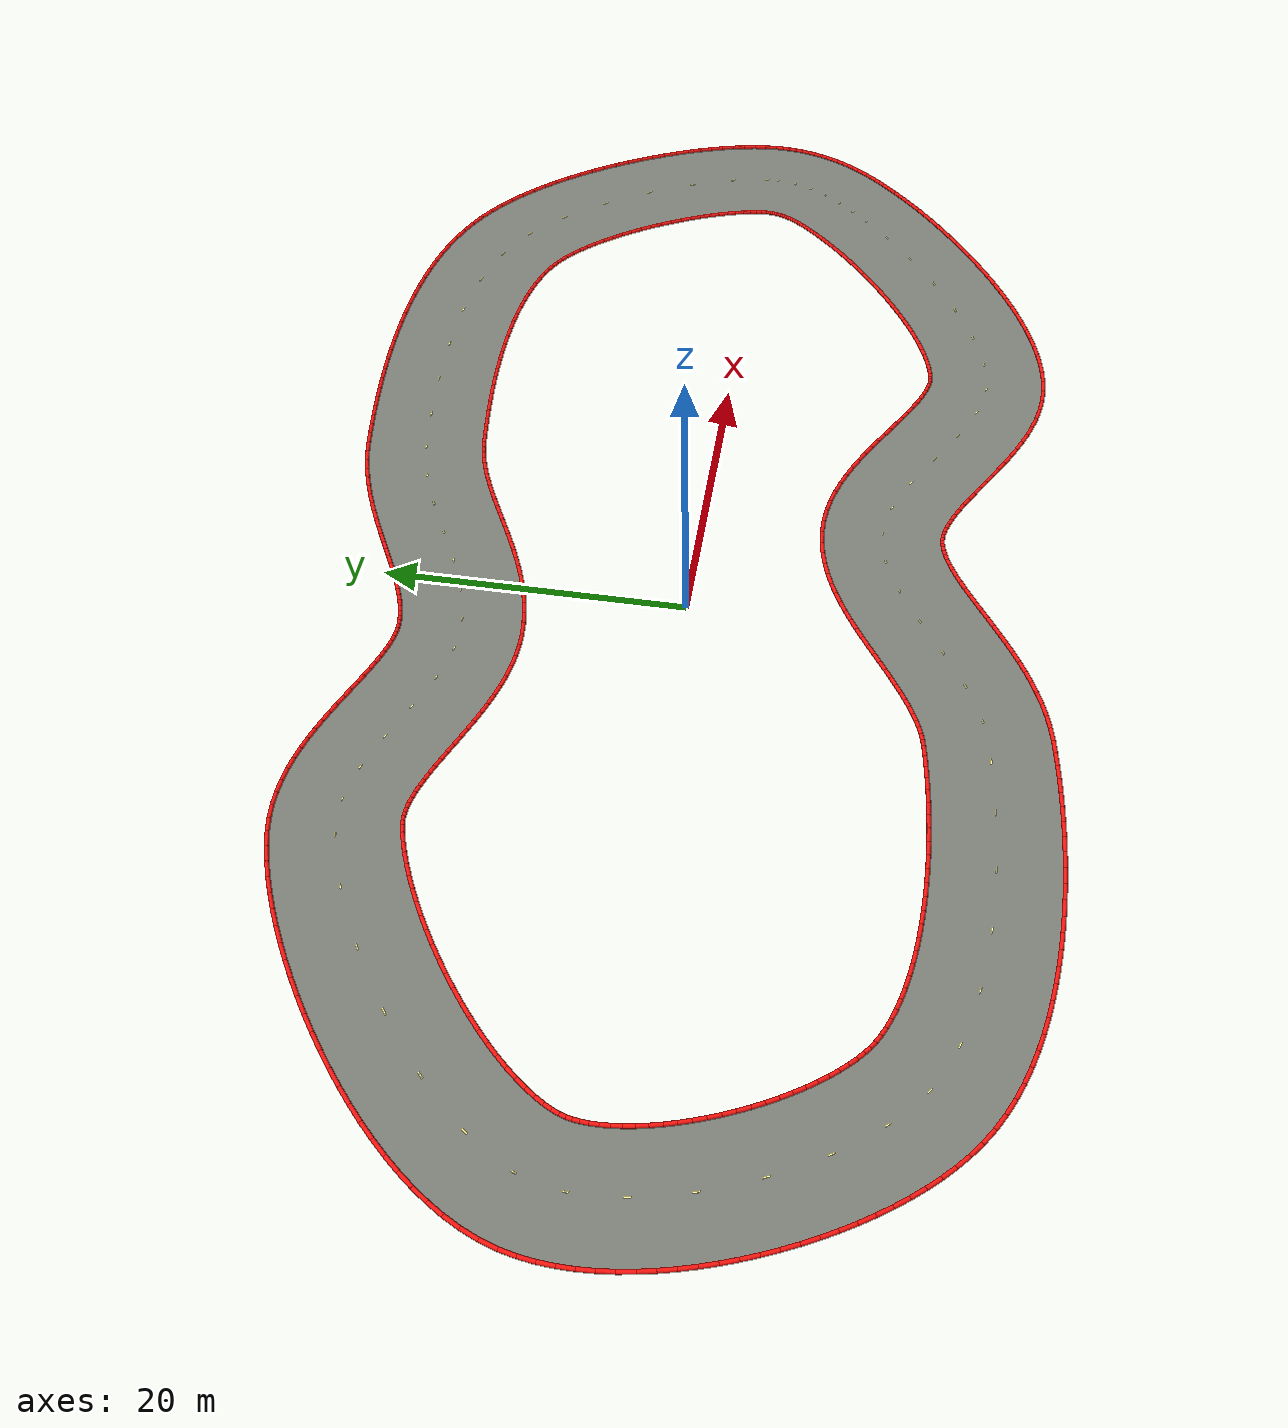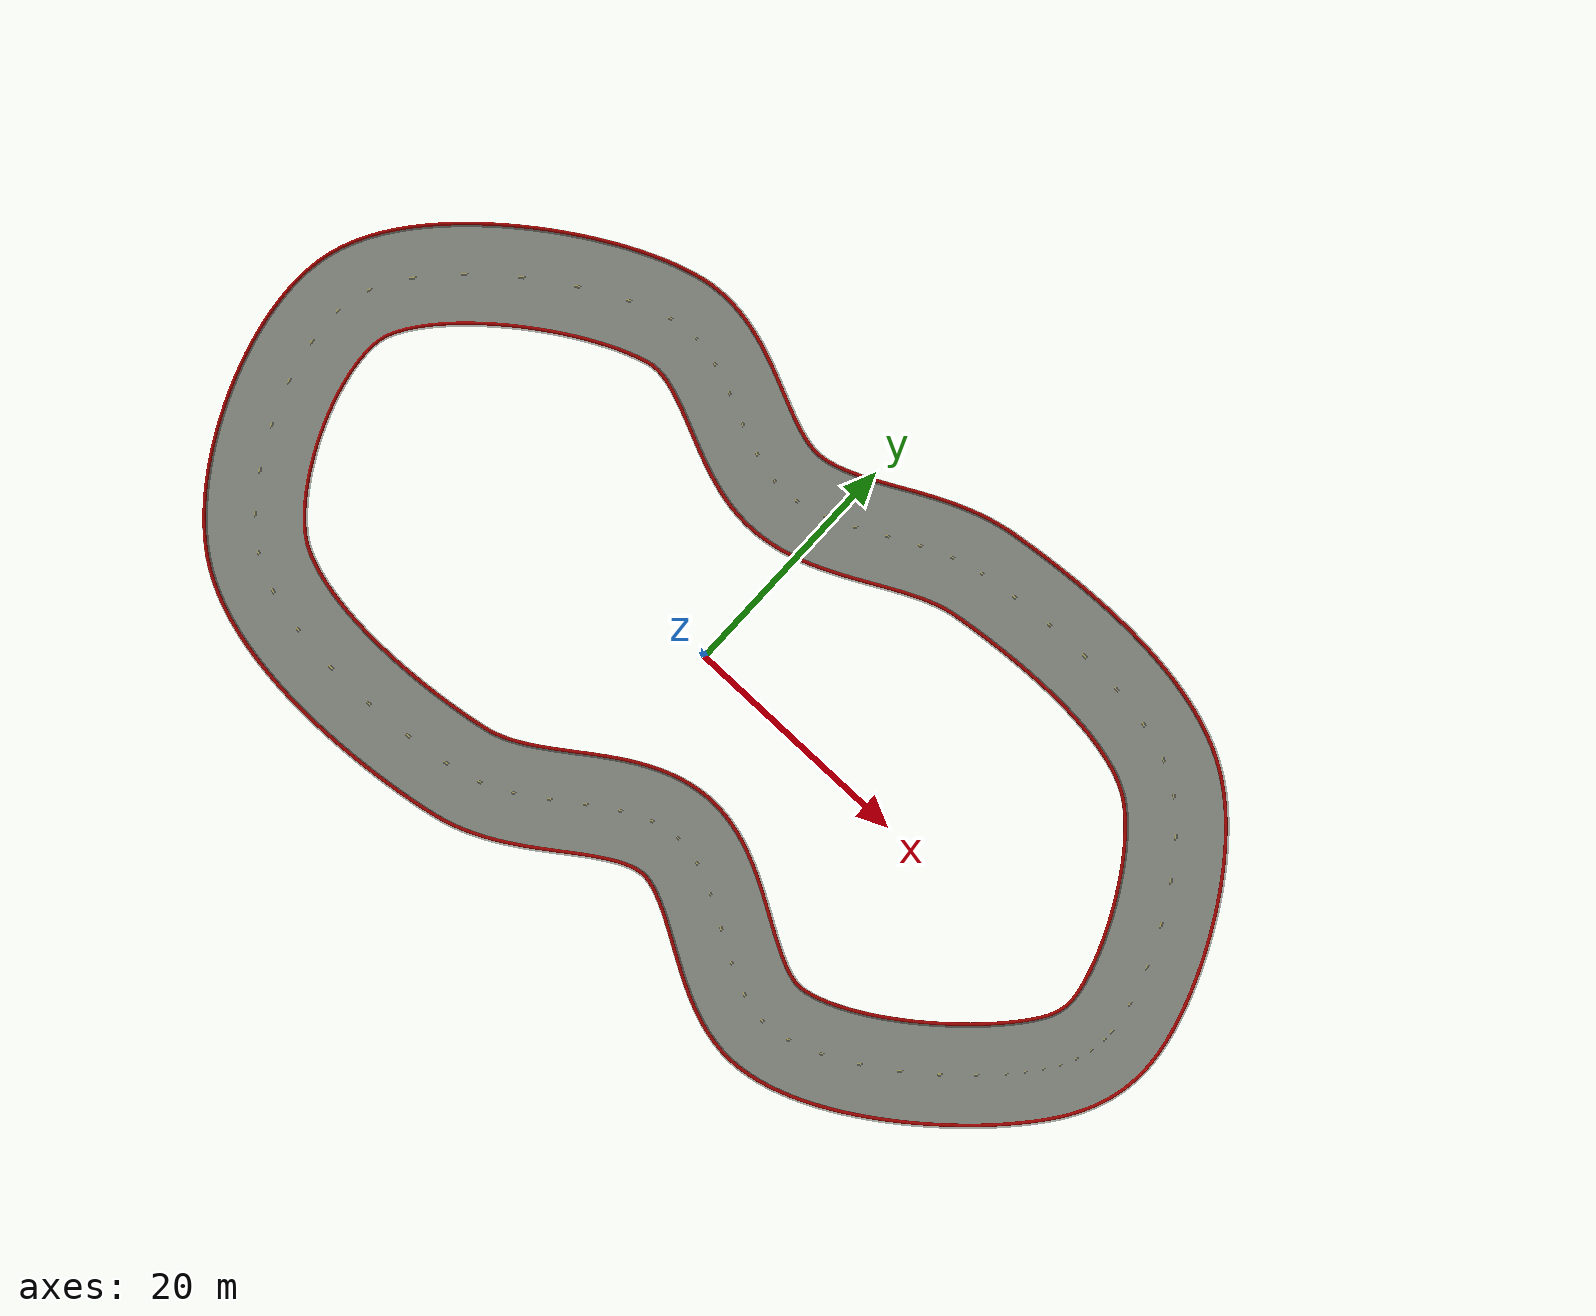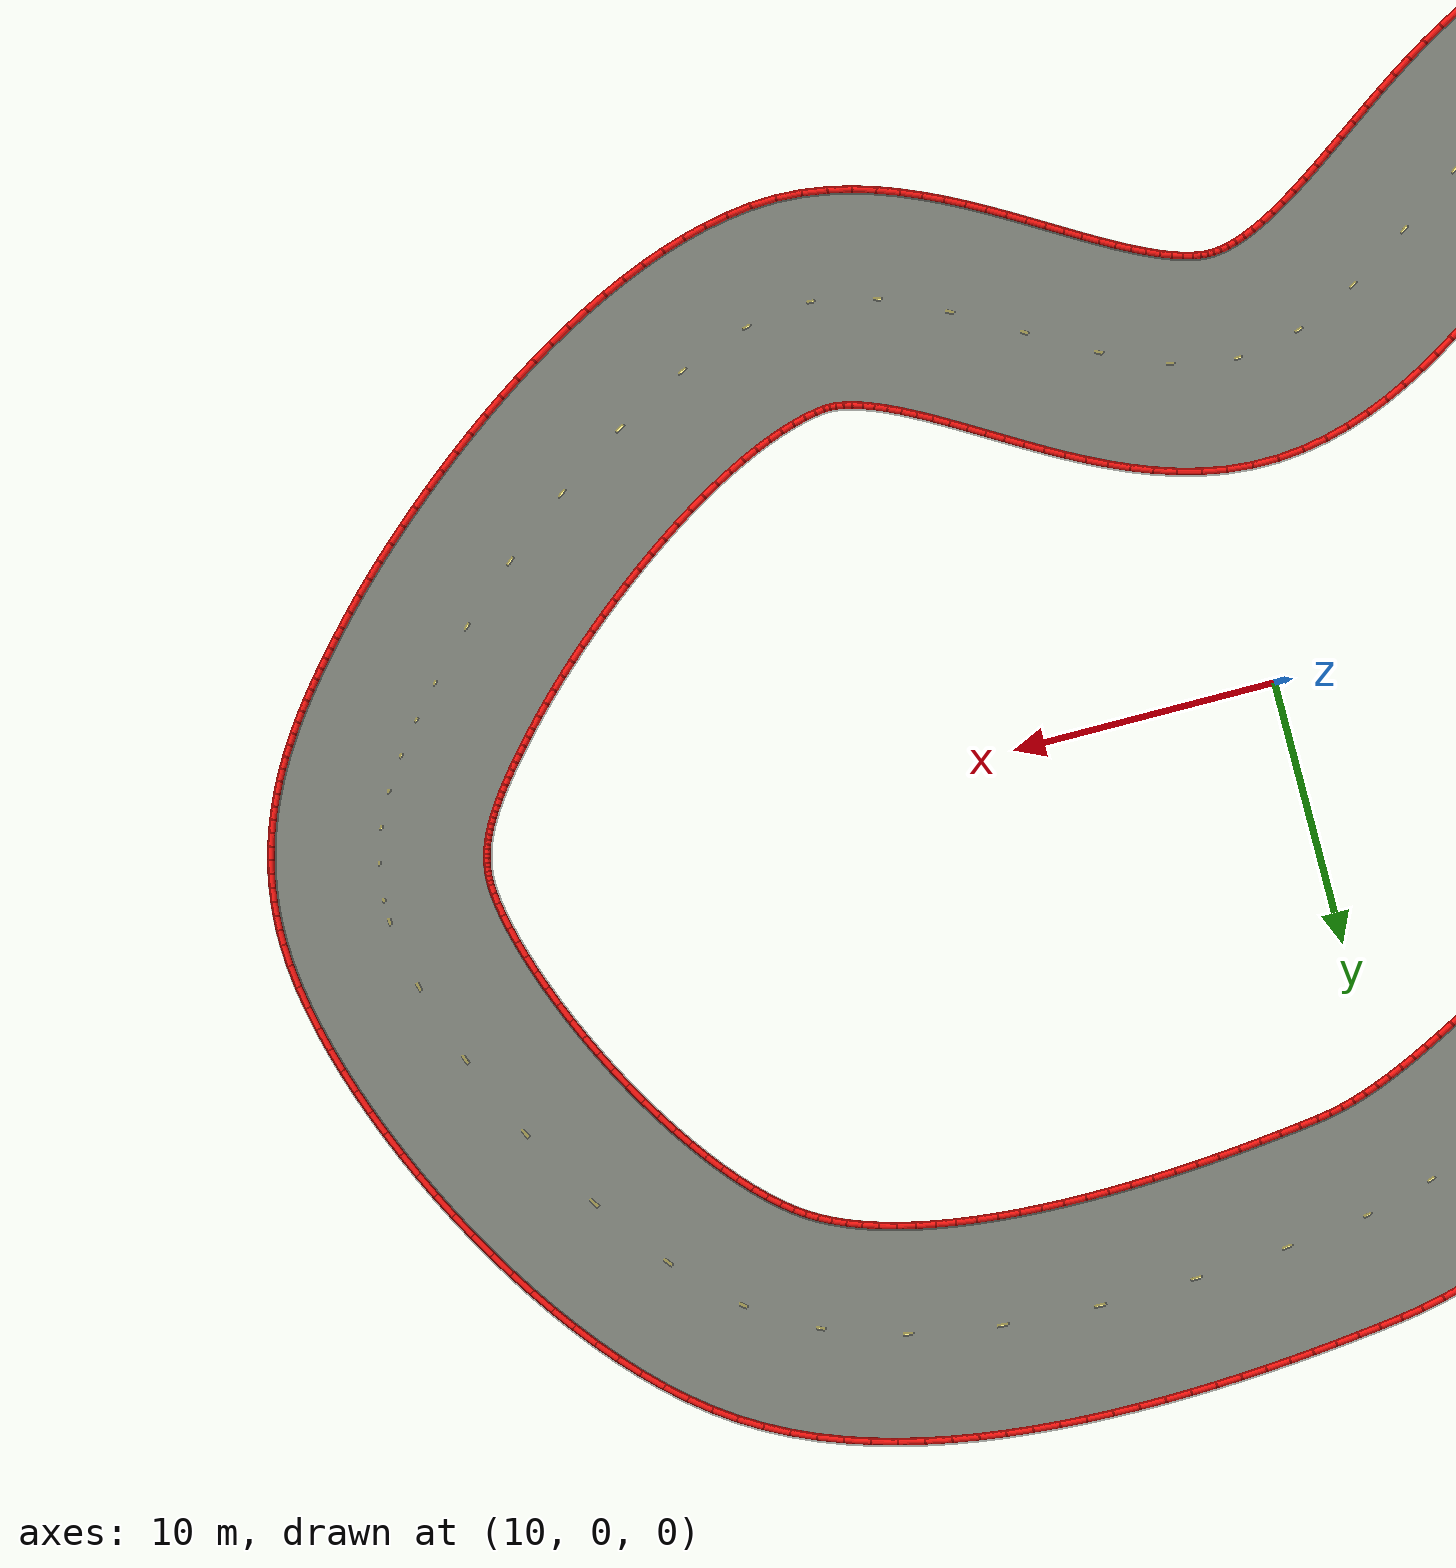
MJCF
<mujoco model="chicane_track_visuals">
  <asset>
    <mesh name="track_surface_mesh" inertia="shell" vertex="40.00154 -0.11086 0.02200 39.98239 0.23497 0.02200 39.93553 0.63349 0.02200 39.85653 1.10161 0.02200 39.74402 1.62753 0.02200 39.59796 2.20140 0.02200 39.41905 2.81484 0.02200 39.20841 3.46053 0.02200 38.96744 4.13187 0.02200 38.69770 4.82280 0.02200 38.40087 5.52769 0.02200 38.07870 6.24115 0.02200 37.73304 6.95803 0.02200 37.36581 7.67332 0.02200 36.97902 8.38209 0.02200 36.57479 9.07949 0.02200 36.15538 9.76070 0.02200 35.72320 10.42094 0.02200 35.28088 11.05541 0.02200 34.83132 11.65933 0.02200 34.37773 12.22789 0.02200 33.92379 12.75637 0.02200 33.47368 13.24008 0.02200 33.03226 13.67457 0.02200 32.60521 14.05572 0.02200 32.19912 14.38006 0.02200 31.81885 14.64700 0.02200 31.40989 14.89319 0.02200 30.95444 15.12819 0.02200 30.44890 15.35221 0.02200 29.89538 15.56272 0.02200 29.29670 15.75762 0.02200 28.65618 15.93529 0.02200 27.97740 16.09463 0.02200 27.26409 16.23492 0.02200 26.52001 16.35584 0.02200 25.74891 16.45739 0.02200 24.95448 16.53980 0.02200 24.14035 16.60352 0.02200 23.31005 16.64916 0.02200 22.46706 16.67748 0.02200 21.61475 16.68933 0.02200 20.75646 16.68564 0.02200 19.89543 16.66742 0.02200 19.03484 16.63574 0.02200 18.17785 16.59170 0.02200 17.32754 16.53643 0.02200 16.48695 16.47111 0.02200 15.65911 16.39692 0.02200 14.84698 16.31507 0.02200 14.05350 16.22678 0.02200 13.28160 16.13329 0.02200 12.57905 16.04213 0.02200 12.07052 15.96043 0.02200 11.60032 15.85903 0.02200 11.11992 15.73161 0.02200 10.62837 15.57863 0.02200 10.12521 15.40083 0.02200 9.61029 15.19929 0.02200 9.08366 14.97542 0.02200 8.54544 14.73093 0.02200 7.99570 14.46781 0.02200 7.43445 14.18827 0.02200 6.86156 13.89473 0.02200 6.27670 13.58977 0.02200 5.67938 13.27610 0.02200 5.06888 12.95660 0.02200 4.44425 12.63424 0.02200 3.80432 12.31220 0.02200 3.14772 11.99380 0.02200 2.47285 11.68261 0.02200 1.77797 11.38249 0.02200 1.06126 11.09766 0.02200 0.32088 10.83278 0.02200 -0.44483 10.59302 0.02200 -1.23713 10.38408 0.02200 -2.05670 10.21219 0.02200 -2.90326 10.08399 0.02200 -3.78949 10.00554 0.02200 -4.69940 9.99114 0.02200 -5.60175 10.04537 0.02200 -6.47180 10.15838 0.02200 -7.30853 10.31957 0.02200 -8.11264 10.51933 0.02200 -8.88585 10.74913 0.02200 -9.63032 11.00153 0.02200 -10.34826 11.26998 0.02200 -11.04167 11.54866 0.02200 -11.71221 11.83228 0.02200 -12.36108 12.11595 0.02200 -12.98902 12.39508 0.02200 -13.59631 12.66534 0.02200 -14.18271 12.92259 0.02200 -14.74752 13.16294 0.02200 -15.28959 13.38279 0.02200 -15.80732 13.57892 0.02200 -16.29876 13.74858 0.02200 -16.76175 13.88974 0.02200 -17.19412 14.00118 0.02200 -17.59409 14.08268 0.02200 -17.96079 14.13510 0.02200 -18.29487 14.16024 0.02200 -18.59926 14.16041 0.02200 -18.87964 14.13764 0.02200 -19.17671 14.08564 0.02200 -19.71830 13.94898 0.02200 -20.35911 13.75216 0.02200 -21.06139 13.50119 0.02200 -21.81346 13.19821 0.02200 -22.60532 12.84600 0.02200 -23.42812 12.44766 0.02200 -24.27386 12.00650 0.02200 -25.13513 11.52592 0.02200 -26.00496 11.00940 0.02200 -26.87668 10.46051 0.02200 -27.74384 9.88284 0.02200 -28.60015 9.28013 0.02200 -29.43940 8.65617 0.02200 -30.25548 8.01494 0.02200 -31.04227 7.36060 0.02200 -31.79371 6.69754 0.02200 -32.50372 6.03051 0.02200 -33.16622 5.36470 0.02200 -33.77521 4.70585 0.02200 -34.32478 4.06049 0.02200 -34.80928 3.43611 0.02200 -35.22358 2.84146 0.02200 -35.56355 2.28681 0.02200 -35.82678 1.78412 0.02200 -36.01382 1.34691 0.02200 -36.13647 0.96408 0.02200 -36.21150 0.61327 0.02200 -36.26948 0.18173 0.02200 -36.30106 -0.31417 0.02200 -36.30169 -0.86732 0.02200 -36.26854 -1.47024 0.02200 -36.20012 -2.11555 0.02200 -36.09596 -2.79612 0.02200 -35.95632 -3.50521 0.02200 -35.78203 -4.23641 0.02200 -35.57432 -4.98363 0.02200 -35.33470 -5.74106 0.02200 -35.06496 -6.50312 0.02200 -34.76706 -7.26440 0.02200 -34.44314 -8.01965 0.02200 -34.09551 -8.76369 0.02200 -33.72664 -9.49145 0.02200 -33.33920 -10.19788 0.02200 -32.93609 -10.87798 0.02200 -32.52048 -11.52674 0.02200 -32.09585 -12.13917 0.02200 -31.66615 -12.71027 0.02200 -31.23584 -13.23511 0.02200 -30.81007 -13.70886 0.02200 -30.39488 -14.12698 0.02200 -29.99732 -14.48537 0.02200 -29.63403 -14.77476 0.02200 -29.24337 -15.03938 0.02200 -28.80090 -15.29097 0.02200 -28.29128 -15.53622 0.02200 -27.71751 -15.77033 0.02200 -27.08380 -15.98939 0.02200 -26.39504 -16.19043 0.02200 -25.65649 -16.37133 0.02200 -24.87350 -16.53070 0.02200 -24.05140 -16.66773 0.02200 -23.19541 -16.78208 0.02200 -22.31067 -16.87378 0.02200 -21.40214 -16.94315 0.02200 -20.47467 -16.99071 0.02200 -19.53301 -17.01718 0.02200 -18.58178 -17.02340 0.02200 -17.62553 -17.01030 0.02200 -16.66871 -16.97893 0.02200 -15.71576 -16.93037 0.02200 -14.77105 -16.86578 0.02200 -13.83893 -16.78637 0.02200 -12.92375 -16.69339 0.02200 -12.02988 -16.58814 0.02200 -11.16171 -16.47197 0.02200 -10.32372 -16.34626 0.02200 -9.52050 -16.21250 0.02200 -8.80600 -16.08205 0.02200 -8.32163 -15.97281 0.02200 -7.87744 -15.84068 0.02200 -7.41856 -15.67443 0.02200 -6.94427 -15.47389 0.02200 -6.45468 -15.23954 0.02200 -5.95040 -14.97259 0.02200 -5.43223 -14.67489 0.02200 -4.90099 -14.34885 0.02200 -4.35731 -13.99731 0.02200 -3.80159 -13.62343 0.02200 -3.23390 -13.23060 0.02200 -2.65398 -12.82237 0.02200 -2.06118 -12.40244 0.02200 -1.45446 -11.97456 0.02200 -0.83235 -11.54262 0.02200 -0.19295 -11.11062 0.02200 0.46612 -10.68277 0.02200 1.14769 -10.26358 0.02200 1.85502 -9.85800 0.02200 2.59174 -9.47163 0.02200 3.36164 -9.11098 0.02200 4.16831 -8.78367 0.02200 5.01466 -8.49867 0.02200 5.90213 -8.26632 0.02200 6.82986 -8.09798 0.02200 7.80291 -8.00486 0.02200 8.78940 -8.00269 0.02200 9.75719 -8.09126 0.02200 10.68294 -8.25571 0.02200 11.56561 -8.48114 0.02200 12.40712 -8.75456 0.02200 13.21096 -9.06508 0.02200 13.98109 -9.40363 0.02200 14.72130 -9.76260 0.02200 15.43492 -10.13540 0.02200 16.12459 -10.51610 0.02200 16.79229 -10.89925 0.02200 17.43930 -11.27962 0.02200 18.06626 -11.65216 0.02200 18.67314 -12.01191 0.02200 19.25929 -12.35402 0.02200 19.82339 -12.67372 0.02200 20.36345 -12.96646 0.02200 20.87677 -13.22800 0.02200 21.35994 -13.45466 0.02200 21.80893 -13.64356 0.02200 22.21927 -13.79307 0.02200 22.58655 -13.90319 0.02200 22.90723 -13.97602 0.02200 23.17992 -14.01583 0.02200 23.40703 -14.02858 0.02200 23.63751 -14.01646 0.02200 23.97942 -13.96854 0.02200 24.39794 -13.88455 0.02200 24.85590 -13.76570 0.02200 25.34790 -13.61143 0.02200 25.86872 -13.42212 0.02200 26.41347 -13.19890 0.02200 26.97762 -12.94339 0.02200 27.55698 -12.65758 0.02200 28.14771 -12.34369 0.02200 28.74622 -12.00414 0.02200 29.34918 -11.64146 0.02200 29.95346 -11.25826 0.02200 30.55611 -10.85720 0.02200 31.15429 -10.44099 0.02200 31.74529 -10.01239 0.02200 32.32646 -9.57416 0.02200 32.89526 -9.12910 0.02200 33.44915 -8.68007 0.02200 33.98564 -8.22993 0.02200 34.50225 -7.78162 0.02200 34.99647 -7.33818 0.02200 35.46577 -6.90270 0.02200 35.90755 -6.47847 0.02200 36.31909 -6.06898 0.02200 36.69753 -5.67801 0.02200 37.05128 -5.29721 0.02200 37.28501 -5.03855 0.02200 37.52094 -4.77393 0.02200 37.74710 -4.51581 0.02200 37.96303 -4.26415 0.02200 38.16829 -4.01892 0.02200 38.36251 -3.78014 0.02200 38.54534 -3.54783 0.02200 38.71654 -3.32204 0.02200 38.87589 -3.10285 0.02200 39.02331 -2.89030 0.02200 39.15877 -2.68445 0.02200 39.28237 -2.48530 0.02200 39.39432 -2.29277 0.02200 39.49493 -2.10672 0.02200 39.58464 -1.92687 0.02200 39.66396 -1.75277 0.02200 39.73348 -1.58380 0.02200 39.79383 -1.41913 0.02200 39.84566 -1.25770 0.02200 39.88954 -1.09821 0.02200 39.92597 -0.93914 0.02200 39.95528 -0.77880 0.02200 39.97762 -0.61534 0.02200 39.99292 -0.44681 0.02200 40.00088 -0.27125 0.02200 47.99846 0.11086 0.02200 47.95293 0.92082 0.02200 47.85599 1.75882 0.02200 47.71493 2.60013 0.02200 47.53396 3.44876 0.02200 47.31596 4.30674 0.02200 47.06308 5.17466 0.02200 46.77703 6.05205 0.02200 46.45926 6.93770 0.02200 46.11105 7.82986 0.02200 45.73357 8.72637 0.02200 45.32790 9.62480 0.02200 44.89505 10.52252 0.02200 44.43594 11.41674 0.02200 43.95140 12.30458 0.02200 43.44214 13.18309 0.02200 42.90877 14.04927 0.02200 42.35170 14.90012 0.02200 41.77115 15.73264 0.02200 41.16707 16.54382 0.02200 40.53908 17.33062 0.02200 39.88636 18.09001 0.02200 39.20756 18.81885 0.02200 38.50066 19.51380 0.02200 37.76284 20.17118 0.02200 36.99034 20.78664 0.02200 36.18115 21.35300 0.02200 35.31331 21.87626 0.02200 34.41530 22.34085 0.02200 33.49614 22.74913 0.02200 32.55917 23.10621 0.02200 31.60697 23.41677 0.02200 30.64167 23.68499 0.02200 29.66509 23.91458 0.02200 28.67896 24.10881 0.02200 27.68492 24.27058 0.02200 26.68466 24.40248 0.02200 25.67992 24.50684 0.02200 24.67250 24.58580 0.02200 23.66429 24.64132 0.02200 22.65724 24.67522 0.02200 21.65339 24.68923 0.02200 20.65486 24.68499 0.02200 19.66383 24.66407 0.02200 18.68252 24.62798 0.02200 17.71323 24.57819 0.02200 16.75829 24.51615 0.02200 15.82009 24.44327 0.02200 14.90104 24.36092 0.02200 14.00359 24.27049 0.02200 13.13023 24.17333 0.02200 12.28347 24.07078 0.02200 11.42095 23.95787 0.02200 10.58766 23.82180 0.02200 9.73427 23.63835 0.02200 8.90815 23.41978 0.02200 8.10907 23.17159 0.02200 7.33634 22.89898 0.02200 6.58891 22.60681 0.02200 5.86559 22.29963 0.02200 5.16509 21.98167 0.02200 4.48615 21.65690 0.02200 3.82760 21.32904 0.02200 3.18842 21.00163 0.02200 2.56774 20.67804 0.02200 1.96491 20.36149 0.02200 1.37947 20.05507 0.02200 0.81120 19.76173 0.02200 0.26010 19.48426 0.02200 -0.27362 19.22529 0.02200 -0.78954 18.98718 0.02200 -1.28709 18.77204 0.02200 -1.76560 18.58157 0.02200 -2.22442 18.41708 0.02200 -2.66305 18.27934 0.02200 -3.08139 18.16860 0.02200 -3.47995 18.08457 0.02200 -3.86015 18.02656 0.02200 -4.21051 17.99446 0.02200 -4.52140 17.98916 0.02200 -4.84128 18.00914 0.02200 -5.19482 18.05580 0.02200 -5.58296 18.13126 0.02200 -6.00492 18.23668 0.02200 -6.45891 18.37212 0.02200 -6.94267 18.53655 0.02200 -7.45392 18.72805 0.02200 -7.99058 18.94398 0.02200 -8.55091 19.18117 0.02200 -9.13362 19.43603 0.02200 -9.73790 19.70468 0.02200 -10.36339 19.98301 0.02200 -11.01025 20.26667 0.02200 -11.67909 20.55109 0.02200 -12.37099 20.83140 0.02200 -13.08746 21.10237 0.02200 -13.83038 21.35826 0.02200 -14.60184 21.59265 0.02200 -15.40390 21.79830 0.02200 -16.23827 21.96695 0.02200 -17.10575 22.08927 0.02200 -18.00560 22.15501 0.02200 -18.93482 22.15337 0.02200 -19.88764 22.07388 0.02200 -20.82329 21.91436 0.02200 -21.86037 21.65687 0.02200 -22.87705 21.34558 0.02200 -23.90081 20.98034 0.02200 -24.93307 20.56489 0.02200 -25.97359 20.10236 0.02200 -27.02096 19.59549 0.02200 -28.07294 19.04688 0.02200 -29.12667 18.45900 0.02200 -30.17887 17.83424 0.02200 -31.22597 17.17494 0.02200 -32.26416 16.48335 0.02200 -33.28948 15.76165 0.02200 -34.29788 15.01189 0.02200 -35.28523 14.23601 0.02200 -36.24737 13.43571 0.02200 -37.18014 12.61247 0.02200 -38.07936 11.76743 0.02200 -38.94084 10.90129 0.02200 -39.76034 10.01417 0.02200 -40.53352 9.10545 0.02200 -41.25577 8.17349 0.02200 -41.92197 7.21544 0.02200 -42.52600 6.22689 0.02200 -43.06001 5.20178 0.02200 -43.51320 4.13247 0.02200 -43.86353 3.03592 0.02200 -44.08961 2.00446 0.02200 -44.22963 0.97923 0.02200 -44.29664 -0.04836 0.02200 -44.29892 -1.07770 0.02200 -44.24304 -2.10851 0.02200 -44.13420 -3.14044 0.02200 -43.97661 -4.17283 0.02200 -43.77372 -5.20470 0.02200 -43.52844 -6.23471 0.02200 -43.24326 -7.26118 0.02200 -42.92039 -8.28220 0.02200 -42.56177 -9.29558 0.02200 -42.16918 -10.29899 0.02200 -41.74418 -11.28993 0.02200 -41.28821 -12.26583 0.02200 -40.80251 -13.22401 0.02200 -40.28814 -14.16176 0.02200 -39.74592 -15.07635 0.02200 -39.17642 -15.96503 0.02200 -38.57987 -16.82505 0.02200 -37.95606 -17.65365 0.02200 -37.30425 -18.44801 0.02200 -36.62300 -19.20522 0.02200 -35.91003 -19.92207 0.02200 -35.16199 -20.59490 0.02200 -34.36597 -21.22524 0.02200 -33.47022 -21.83157 0.02200 -32.52193 -22.37291 0.02200 -31.54388 -22.84516 0.02200 -30.54053 -23.25569 0.02200 -29.51511 -23.61098 0.02200 -28.47016 -23.91661 0.02200 -27.40789 -24.17726 0.02200 -26.33039 -24.39692 0.02200 -25.23978 -24.57897 0.02200 -24.13827 -24.72632 0.02200 -23.02819 -24.84154 0.02200 -21.91200 -24.92688 0.02200 -20.79231 -24.98440 0.02200 -19.67182 -25.01598 0.02200 -18.55335 -25.02335 0.02200 -17.43981 -25.00815 0.02200 -16.33417 -24.97193 0.02200 -15.23946 -24.91618 0.02200 -14.15875 -24.84231 0.02200 -13.09513 -24.75172 0.02200 -12.05170 -24.64572 0.02200 -11.03155 -24.52561 0.02200 -10.03771 -24.39261 0.02200 -9.07316 -24.24791 0.02200 -8.14076 -24.09262 0.02200 -7.19400 -23.91795 0.02200 -6.29392 -23.71158 0.02200 -5.37882 -23.44048 0.02200 -4.50196 -23.12382 0.02200 -3.66246 -22.76976 0.02200 -2.85860 -22.38574 0.02200 -2.08816 -21.97852 0.02200 -1.34871 -21.55420 0.02200 -0.63786 -21.11833 0.02200 0.04665 -20.67602 0.02200 0.70683 -20.23207 0.02200 1.34436 -19.79105 0.02200 1.96057 -19.35735 0.02200 2.55644 -18.93524 0.02200 3.13252 -18.52891 0.02200 3.68896 -18.14244 0.02200 4.22546 -17.77977 0.02200 4.74127 -17.44466 0.02200 5.23515 -17.14055 0.02200 5.70544 -16.87044 0.02200 6.15013 -16.63668 0.02200 6.56704 -16.44074 0.02200 6.95419 -16.28293 0.02200 7.31027 -16.16224 0.02200 7.63546 -16.07629 0.02200 7.93221 -16.02167 0.02200 8.19709 -15.99514 0.02200 8.42971 -15.99460 0.02200 8.68501 -16.01909 0.02200 8.98593 -16.07365 0.02200 9.33315 -16.16334 0.02200 9.72434 -16.29132 0.02200 10.15567 -16.45867 0.02200 10.62278 -16.66461 0.02200 11.12149 -16.90693 0.02200 11.64812 -17.18239 0.02200 12.19962 -17.48709 0.02200 12.77365 -17.81666 0.02200 13.36854 -18.16648 0.02200 13.98328 -18.53179 0.02200 14.61750 -18.90770 0.02200 15.27149 -19.28926 0.02200 15.94619 -19.67138 0.02200 16.64319 -20.04881 0.02200 17.36484 -20.41593 0.02200 18.11415 -20.76662 0.02200 18.89478 -21.09391 0.02200 19.71081 -21.38962 0.02200 20.56628 -21.64390 0.02200 21.46435 -21.84483 0.02200 22.40602 -21.97831 0.02200 23.38851 -22.02856 0.02200 24.36249 -21.98354 0.02200 25.29813 -21.85911 0.02200 26.18411 -21.68261 0.02200 27.05376 -21.45787 0.02200 27.90864 -21.19052 0.02200 28.75014 -20.88519 0.02200 29.57932 -20.54584 0.02200 30.39686 -20.17588 0.02200 31.20312 -19.77837 0.02200 31.99811 -19.35614 0.02200 32.78157 -18.91181 0.02200 33.55300 -18.44792 0.02200 34.31169 -17.96690 0.02200 35.05677 -17.47113 0.02200 35.78723 -16.96295 0.02200 36.50195 -16.44466 0.02200 37.19972 -15.91855 0.02200 37.87929 -15.38685 0.02200 38.53933 -14.85178 0.02200 39.17849 -14.31551 0.02200 39.79544 -13.78013 0.02200 40.38883 -13.24769 0.02200 40.95737 -12.72012 0.02200 41.49982 -12.19919 0.02200 42.01505 -11.68646 0.02200 42.50210 -11.18319 0.02200 42.94872 -10.70279 0.02200 43.23812 -10.38276 0.02200 43.51544 -10.07166 0.02200 43.79172 -9.75628 0.02200 44.06652 -9.43593 0.02200 44.33935 -9.10990 0.02200 44.60966 -8.77745 0.02200 44.87687 -8.43779 0.02200 45.14033 -8.09015 0.02200 45.39932 -7.73372 0.02200 45.65301 -7.36770 0.02200 45.90050 -6.99131 0.02200 46.14077 -6.60382 0.02200 46.37271 -6.20455 0.02200 46.59507 -5.79292 0.02200 46.80650 -5.36848 0.02200 47.00558 -4.93091 0.02200 47.19078 -4.48012 0.02200 47.36056 -4.01619 0.02200 47.51336 -3.53946 0.02200 47.64768 -3.05047 0.02200 47.76211 -2.55001 0.02200 47.85539 -2.03904 0.02200 47.92645 -1.51867 0.02200 47.97445 -0.99011 0.02200 47.99878 -0.45457 0.02200" face="0 287 1 0 286 287 1 288 2 1 287 288 2 289 3 2 288 289 3 290 4 3 289 290 4 291 5 4 290 291 5 292 6 5 291 292 6 293 7 6 292 293 7 294 8 7 293 294 8 295 9 8 294 295 9 296 10 9 295 296 10 297 11 10 296 297 11 298 12 11 297 298 12 299 13 12 298 299 13 300 14 13 299 300 14 301 15 14 300 301 15 302 16 15 301 302 16 303 17 16 302 303 17 304 18 17 303 304 18 305 19 18 304 305 19 306 20 19 305 306 20 307 21 20 306 307 21 308 22 21 307 308 22 309 23 22 308 309 23 310 24 23 309 310 24 311 25 24 310 311 25 312 26 25 311 312 26 313 27 26 312 313 27 314 28 27 313 314 28 315 29 28 314 315 29 316 30 29 315 316 30 317 31 30 316 317 31 318 32 31 317 318 32 319 33 32 318 319 33 320 34 33 319 320 34 321 35 34 320 321 35 322 36 35 321 322 36 323 37 36 322 323 37 324 38 37 323 324 38 325 39 38 324 325 39 326 40 39 325 326 40 327 41 40 326 327 41 328 42 41 327 328 42 329 43 42 328 329 43 330 44 43 329 330 44 331 45 44 330 331 45 332 46 45 331 332 46 333 47 46 332 333 47 334 48 47 333 334 48 335 49 48 334 335 49 336 50 49 335 336 50 337 51 50 336 337 51 338 52 51 337 338 52 339 53 52 338 339 53 340 54 53 339 340 54 341 55 54 340 341 55 342 56 55 341 342 56 343 57 56 342 343 57 344 58 57 343 344 58 345 59 58 344 345 59 346 60 59 345 346 60 347 61 60 346 347 61 348 62 61 347 348 62 349 63 62 348 349 63 350 64 63 349 350 64 351 65 64 350 351 65 352 66 65 351 352 66 353 67 66 352 353 67 354 68 67 353 354 68 355 69 68 354 355 69 356 70 69 355 356 70 357 71 70 356 357 71 358 72 71 357 358 72 359 73 72 358 359 73 360 74 73 359 360 74 361 75 74 360 361 75 362 76 75 361 362 76 363 77 76 362 363 77 364 78 77 363 364 78 365 79 78 364 365 79 366 80 79 365 366 80 367 81 80 366 367 81 368 82 81 367 368 82 369 83 82 368 369 83 370 84 83 369 370 84 371 85 84 370 371 85 372 86 85 371 372 86 373 87 86 372 373 87 374 88 87 373 374 88 375 89 88 374 375 89 376 90 89 375 376 90 377 91 90 376 377 91 378 92 91 377 378 92 379 93 92 378 379 93 380 94 93 379 380 94 381 95 94 380 381 95 382 96 95 381 382 96 383 97 96 382 383 97 384 98 97 383 384 98 385 99 98 384 385 99 386 100 99 385 386 100 387 101 100 386 387 101 388 102 101 387 388 102 389 103 102 388 389 103 390 104 103 389 390 104 391 105 104 390 391 105 392 106 105 391 392 106 393 107 106 392 393 107 394 108 107 393 394 108 395 109 108 394 395 109 396 110 109 395 396 110 397 111 110 396 397 111 398 112 111 397 398 112 399 113 112 398 399 113 400 114 113 399 400 114 401 115 114 400 401 115 402 116 115 401 402 116 403 117 116 402 403 117 404 118 117 403 404 118 405 119 118 404 405 119 406 120 119 405 406 120 407 121 120 406 407 121 408 122 121 407 408 122 409 123 122 408 409 123 410 124 123 409 410 124 411 125 124 410 411 125 412 126 125 411 412 126 413 127 126 412 413 127 414 128 127 413 414 128 415 129 128 414 415 129 416 130 129 415 416 130 417 131 130 416 417 131 418 132 131 417 418 132 419 133 132 418 419 133 420 134 133 419 420 134 421 135 134 420 421 135 422 136 135 421 422 136 423 137 136 422 423 137 424 138 137 423 424 138 425 139 138 424 425 139 426 140 139 425 426 140 427 141 140 426 427 141 428 142 141 427 428 142 429 143 142 428 429 143 430 144 143 429 430 144 431 145 144 430 431 145 432 146 145 431 432 146 433 147 146 432 433 147 434 148 147 433 434 148 435 149 148 434 435 149 436 150 149 435 436 150 437 151 150 436 437 151 438 152 151 437 438 152 439 153 152 438 439 153 440 154 153 439 440 154 441 155 154 440 441 155 442 156 155 441 442 156 443 157 156 442 443 157 444 158 157 443 444 158 445 159 158 444 445 159 446 160 159 445 446 160 447 161 160 446 447 161 448 162 161 447 448 162 449 163 162 448 449 163 450 164 163 449 450 164 451 165 164 450 451 165 452 166 165 451 452 166 453 167 166 452 453 167 454 168 167 453 454 168 455 169 168 454 455 169 456 170 169 455 456 170 457 171 170 456 457 171 458 172 171 457 458 172 459 173 172 458 459 173 460 174 173 459 460 174 461 175 174 460 461 175 462 176 175 461 462 176 463 177 176 462 463 177 464 178 177 463 464 178 465 179 178 464 465 179 466 180 179 465 466 180 467 181 180 466 467 181 468 182 181 467 468 182 469 183 182 468 469 183 470 184 183 469 470 184 471 185 184 470 471 185 472 186 185 471 472 186 473 187 186 472 473 187 474 188 187 473 474 188 475 189 188 474 475 189 476 190 189 475 476 190 477 191 190 476 477 191 478 192 191 477 478 192 479 193 192 478 479 193 480 194 193 479 480 194 481 195 194 480 481 195 482 196 195 481 482 196 483 197 196 482 483 197 484 198 197 483 484 198 485 199 198 484 485 199 486 200 199 485 486 200 487 201 200 486 487 201 488 202 201 487 488 202 489 203 202 488 489 203 490 204 203 489 490 204 491 205 204 490 491 205 492 206 205 491 492 206 493 207 206 492 493 207 494 208 207 493 494 208 495 209 208 494 495 209 496 210 209 495 496 210 497 211 210 496 497 211 498 212 211 497 498 212 499 213 212 498 499 213 500 214 213 499 500 214 501 215 214 500 501 215 502 216 215 501 502 216 503 217 216 502 503 217 504 218 217 503 504 218 505 219 218 504 505 219 506 220 219 505 506 220 507 221 220 506 507 221 508 222 221 507 508 222 509 223 222 508 509 223 510 224 223 509 510 224 511 225 224 510 511 225 512 226 225 511 512 226 513 227 226 512 513 227 514 228 227 513 514 228 515 229 228 514 515 229 516 230 229 515 516 230 517 231 230 516 517 231 518 232 231 517 518 232 519 233 232 518 519 233 520 234 233 519 520 234 521 235 234 520 521 235 522 236 235 521 522 236 523 237 236 522 523 237 524 238 237 523 524 238 525 239 238 524 525 239 526 240 239 525 526 240 527 241 240 526 527 241 528 242 241 527 528 242 529 243 242 528 529 243 530 244 243 529 530 244 531 245 244 530 531 245 532 246 245 531 532 246 533 247 246 532 533 247 534 248 247 533 534 248 535 249 248 534 535 249 536 250 249 535 536 250 537 251 250 536 537 251 538 252 251 537 538 252 539 253 252 538 539 253 540 254 253 539 540 254 541 255 254 540 541 255 542 256 255 541 542 256 543 257 256 542 543 257 544 258 257 543 544 258 545 259 258 544 545 259 546 260 259 545 546 260 547 261 260 546 547 261 548 262 261 547 548 262 549 263 262 548 549 263 550 264 263 549 550 264 551 265 264 550 551 265 552 266 265 551 552 266 553 267 266 552 553 267 554 268 267 553 554 268 555 269 268 554 555 269 556 270 269 555 556 270 557 271 270 556 557 271 558 272 271 557 558 272 559 273 272 558 559 273 560 274 273 559 560 274 561 275 274 560 561 275 562 276 275 561 562 276 563 277 276 562 563 277 564 278 277 563 564 278 565 279 278 564 565 279 566 280 279 565 566 280 567 281 280 566 567 281 568 282 281 567 568 282 569 283 282 568 569 283 570 284 283 569 570 284 571 285 284 570 571 285 286 0 285 571 286"/>
    <material name="track_asphalt" rgba="0.48 0.49 0.46 1" emission="0.08"/>
    <material name="track_boundary" rgba="0.95 0.08 0.06 1" emission="0.05"/>
    <material name="track_centerline" rgba="1.0 0.95 0.55 1" emission="0.15"/>
  </asset>
  <worldbody>
    <geom name="track_surface" type="mesh" mesh="track_surface_mesh" material="track_asphalt" contype="0" conaffinity="0"/>
    <geom name="track_left_boundary_000" type="capsule" fromto="40.00154 -0.11086 0.09 39.98239 0.23497 0.09" size="0.14" material="track_boundary" contype="0" conaffinity="0"/>
    <geom name="track_left_boundary_001" type="capsule" fromto="39.98239 0.23497 0.09 39.93553 0.63349 0.09" size="0.14" material="track_boundary" contype="0" conaffinity="0"/>
    <geom name="track_left_boundary_002" type="capsule" fromto="39.93553 0.63349 0.09 39.85653 1.10161 0.09" size="0.14" material="track_boundary" contype="0" conaffinity="0"/>
    <geom name="track_left_boundary_003" type="capsule" fromto="39.85653 1.10161 0.09 39.74402 1.62753 0.09" size="0.14" material="track_boundary" contype="0" conaffinity="0"/>
    <geom name="track_left_boundary_004" type="capsule" fromto="39.74402 1.62753 0.09 39.59796 2.20140 0.09" size="0.14" material="track_boundary" contype="0" conaffinity="0"/>
    <geom name="track_left_boundary_005" type="capsule" fromto="39.59796 2.20140 0.09 39.41905 2.81484 0.09" size="0.14" material="track_boundary" contype="0" conaffinity="0"/>
    <geom name="track_left_boundary_006" type="capsule" fromto="39.41905 2.81484 0.09 39.20841 3.46053 0.09" size="0.14" material="track_boundary" contype="0" conaffinity="0"/>
    <geom name="track_left_boundary_007" type="capsule" fromto="39.20841 3.46053 0.09 38.96744 4.13187 0.09" size="0.14" material="track_boundary" contype="0" conaffinity="0"/>
    <geom name="track_left_boundary_008" type="capsule" fromto="38.96744 4.13187 0.09 38.69770 4.82280 0.09" size="0.14" material="track_boundary" contype="0" conaffinity="0"/>
    <geom name="track_left_boundary_009" type="capsule" fromto="38.69770 4.82280 0.09 38.40087 5.52769 0.09" size="0.14" material="track_boundary" contype="0" conaffinity="0"/>
    <geom name="track_left_boundary_010" type="capsule" fromto="38.40087 5.52769 0.09 38.07870 6.24115 0.09" size="0.14" material="track_boundary" contype="0" conaffinity="0"/>
    <geom name="track_left_boundary_011" type="capsule" fromto="38.07870 6.24115 0.09 37.73304 6.95803 0.09" size="0.14" material="track_boundary" contype="0" conaffinity="0"/>
    <geom name="track_left_boundary_012" type="capsule" fromto="37.73304 6.95803 0.09 37.36581 7.67332 0.09" size="0.14" material="track_boundary" contype="0" conaffinity="0"/>
    <geom name="track_left_boundary_013" type="capsule" fromto="37.36581 7.67332 0.09 36.97902 8.38209 0.09" size="0.14" material="track_boundary" contype="0" conaffinity="0"/>
    <geom name="track_left_boundary_014" type="capsule" fromto="36.97902 8.38209 0.09 36.57479 9.07949 0.09" size="0.14" material="track_boundary" contype="0" conaffinity="0"/>
    <geom name="track_left_boundary_015" type="capsule" fromto="36.57479 9.07949 0.09 36.15538 9.76070 0.09" size="0.14" material="track_boundary" contype="0" conaffinity="0"/>
    <geom name="track_left_boundary_016" type="capsule" fromto="36.15538 9.76070 0.09 35.72320 10.42094 0.09" size="0.14" material="track_boundary" contype="0" conaffinity="0"/>
    <geom name="track_left_boundary_017" type="capsule" fromto="35.72320 10.42094 0.09 35.28088 11.05541 0.09" size="0.14" material="track_boundary" contype="0" conaffinity="0"/>
    <geom name="track_left_boundary_018" type="capsule" fromto="35.28088 11.05541 0.09 34.83132 11.65933 0.09" size="0.14" material="track_boundary" contype="0" conaffinity="0"/>
    <geom name="track_left_boundary_019" type="capsule" fromto="34.83132 11.65933 0.09 34.37773 12.22789 0.09" size="0.14" material="track_boundary" contype="0" conaffinity="0"/>
    <geom name="track_left_boundary_020" type="capsule" fromto="34.37773 12.22789 0.09 33.92379 12.75637 0.09" size="0.14" material="track_boundary" contype="0" conaffinity="0"/>
    <geom name="track_left_boundary_021" type="capsule" fromto="33.92379 12.75637 0.09 33.47368 13.24008 0.09" size="0.14" material="track_boundary" contype="0" conaffinity="0"/>
    <geom name="track_left_boundary_022" type="capsule" fromto="33.47368 13.24008 0.09 33.03226 13.67457 0.09" size="0.14" material="track_boundary" contype="0" conaffinity="0"/>
    <geom name="track_left_boundary_023" type="capsule" fromto="33.03226 13.67457 0.09 32.60521 14.05572 0.09" size="0.14" material="track_boundary" contype="0" conaffinity="0"/>
    <geom name="track_left_boundary_024" type="capsule" fromto="32.60521 14.05572 0.09 32.19912 14.38006 0.09" size="0.14" material="track_boundary" contype="0" conaffinity="0"/>
    <geom name="track_left_boundary_025" type="capsule" fromto="32.19912 14.38006 0.09 31.81885 14.64700 0.09" size="0.14" material="track_boundary" contype="0" conaffinity="0"/>
    <geom name="track_left_boundary_026" type="capsule" fromto="31.81885 14.64700 0.09 31.40989 14.89319 0.09" size="0.14" material="track_boundary" contype="0" conaffinity="0"/>
    <geom name="track_left_boundary_027" type="capsule" fromto="31.40989 14.89319 0.09 30.95444 15.12819 0.09" size="0.14" material="track_boundary" contype="0" conaffinity="0"/>
    <geom name="track_left_boundary_028" type="capsule" fromto="30.95444 15.12819 0.09 30.44890 15.35221 0.09" size="0.14" material="track_boundary" contype="0" conaffinity="0"/>
    <geom name="track_left_boundary_029" type="capsule" fromto="30.44890 15.35221 0.09 29.89538 15.56272 0.09" size="0.14" material="track_boundary" contype="0" conaffinity="0"/>
    <geom name="track_left_boundary_030" type="capsule" fromto="29.89538 15.56272 0.09 29.29670 15.75762 0.09" size="0.14" material="track_boundary" contype="0" conaffinity="0"/>
    <geom name="track_left_boundary_031" type="capsule" fromto="29.29670 15.75762 0.09 28.65618 15.93529 0.09" size="0.14" material="track_boundary" contype="0" conaffinity="0"/>
    <geom name="track_left_boundary_032" type="capsule" fromto="28.65618 15.93529 0.09 27.97740 16.09463 0.09" size="0.14" material="track_boundary" contype="0" conaffinity="0"/>
    <geom name="track_left_boundary_033" type="capsule" fromto="27.97740 16.09463 0.09 27.26409 16.23492 0.09" size="0.14" material="track_boundary" contype="0" conaffinity="0"/>
    <geom name="track_left_boundary_034" type="capsule" fromto="27.26409 16.23492 0.09 26.52001 16.35584 0.09" size="0.14" material="track_boundary" contype="0" conaffinity="0"/>
    <geom name="track_left_boundary_035" type="capsule" fromto="26.52001 16.35584 0.09 25.74891 16.45739 0.09" size="0.14" material="track_boundary" contype="0" conaffinity="0"/>
    <geom name="track_left_boundary_036" type="capsule" fromto="25.74891 16.45739 0.09 24.95448 16.53980 0.09" size="0.14" material="track_boundary" contype="0" conaffinity="0"/>
    <geom name="track_left_boundary_037" type="capsule" fromto="24.95448 16.53980 0.09 24.14035 16.60352 0.09" size="0.14" material="track_boundary" contype="0" conaffinity="0"/>
    <geom name="track_left_boundary_038" type="capsule" fromto="24.14035 16.60352 0.09 23.31005 16.64916 0.09" size="0.14" material="track_boundary" contype="0" conaffinity="0"/>
    <geom name="track_left_boundary_039" type="capsule" fromto="23.31005 16.64916 0.09 22.46706 16.67748 0.09" size="0.14" material="track_boundary" contype="0" conaffinity="0"/>
    <geom name="track_left_boundary_040" type="capsule" fromto="22.46706 16.67748 0.09 21.61475 16.68933 0.09" size="0.14" material="track_boundary" contype="0" conaffinity="0"/>
    <geom name="track_left_boundary_041" type="capsule" fromto="21.61475 16.68933 0.09 20.75646 16.68564 0.09" size="0.14" material="track_boundary" contype="0" conaffinity="0"/>
    <geom name="track_left_boundary_042" type="capsule" fromto="20.75646 16.68564 0.09 19.89543 16.66742 0.09" size="0.14" material="track_boundary" contype="0" conaffinity="0"/>
    <geom name="track_left_boundary_043" type="capsule" fromto="19.89543 16.66742 0.09 19.03484 16.63574 0.09" size="0.14" material="track_boundary" contype="0" conaffinity="0"/>
    <geom name="track_left_boundary_044" type="capsule" fromto="19.03484 16.63574 0.09 18.17785 16.59170 0.09" size="0.14" material="track_boundary" contype="0" conaffinity="0"/>
    <geom name="track_left_boundary_045" type="capsule" fromto="18.17785 16.59170 0.09 17.32754 16.53643 0.09" size="0.14" material="track_boundary" contype="0" conaffinity="0"/>
    <geom name="track_left_boundary_046" type="capsule" fromto="17.32754 16.53643 0.09 16.48695 16.47111 0.09" size="0.14" material="track_boundary" contype="0" conaffinity="0"/>
    <geom name="track_left_boundary_047" type="capsule" fromto="16.48695 16.47111 0.09 15.65911 16.39692 0.09" size="0.14" material="track_boundary" contype="0" conaffinity="0"/>
    <geom name="track_left_boundary_048" type="capsule" fromto="15.65911 16.39692 0.09 14.84698 16.31507 0.09" size="0.14" material="track_boundary" contype="0" conaffinity="0"/>
    <geom name="track_left_boundary_049" type="capsule" fromto="14.84698 16.31507 0.09 14.05350 16.22678 0.09" size="0.14" material="track_boundary" contype="0" conaffinity="0"/>
    <geom name="track_left_boundary_050" type="capsule" fromto="14.05350 16.22678 0.09 13.28160 16.13329 0.09" size="0.14" material="track_boundary" contype="0" conaffinity="0"/>
    <geom name="track_left_boundary_051" type="capsule" fromto="13.28160 16.13329 0.09 12.57905 16.04213 0.09" size="0.14" material="track_boundary" contype="0" conaffinity="0"/>
    <geom name="track_left_boundary_052" type="capsule" fromto="12.57905 16.04213 0.09 12.07052 15.96043 0.09" size="0.14" material="track_boundary" contype="0" conaffinity="0"/>
    <geom name="track_left_boundary_053" type="capsule" fromto="12.07052 15.96043 0.09 11.60032 15.85903 0.09" size="0.14" material="track_boundary" contype="0" conaffinity="0"/>
    <geom name="track_left_boundary_054" type="capsule" fromto="11.60032 15.85903 0.09 11.11992 15.73161 0.09" size="0.14" material="track_boundary" contype="0" conaffinity="0"/>
    <geom name="track_left_boundary_055" type="capsule" fromto="11.11992 15.73161 0.09 10.62837 15.57863 0.09" size="0.14" material="track_boundary" contype="0" conaffinity="0"/>
    <geom name="track_left_boundary_056" type="capsule" fromto="10.62837 15.57863 0.09 10.12521 15.40083 0.09" size="0.14" material="track_boundary" contype="0" conaffinity="0"/>
    <geom name="track_left_boundary_057" type="capsule" fromto="10.12521 15.40083 0.09 9.61029 15.19929 0.09" size="0.14" material="track_boundary" contype="0" conaffinity="0"/>
    <geom name="track_left_boundary_058" type="capsule" fromto="9.61029 15.19929 0.09 9.08366 14.97542 0.09" size="0.14" material="track_boundary" contype="0" conaffinity="0"/>
    <geom name="track_left_boundary_059" type="capsule" fromto="9.08366 14.97542 0.09 8.54544 14.73093 0.09" size="0.14" material="track_boundary" contype="0" conaffinity="0"/>
    <geom name="track_left_boundary_060" type="capsule" fromto="8.54544 14.73093 0.09 7.99570 14.46781 0.09" size="0.14" material="track_boundary" contype="0" conaffinity="0"/>
    <geom name="track_left_boundary_061" type="capsule" fromto="7.99570 14.46781 0.09 7.43445 14.18827 0.09" size="0.14" material="track_boundary" contype="0" conaffinity="0"/>
    <geom name="track_left_boundary_062" type="capsule" fromto="7.43445 14.18827 0.09 6.86156 13.89473 0.09" size="0.14" material="track_boundary" contype="0" conaffinity="0"/>
    <geom name="track_left_boundary_063" type="capsule" fromto="6.86156 13.89473 0.09 6.27670 13.58977 0.09" size="0.14" material="track_boundary" contype="0" conaffinity="0"/>
    <geom name="track_left_boundary_064" type="capsule" fromto="6.27670 13.58977 0.09 5.67938 13.27610 0.09" size="0.14" material="track_boundary" contype="0" conaffinity="0"/>
    <geom name="track_left_boundary_065" type="capsule" fromto="5.67938 13.27610 0.09 5.06888 12.95660 0.09" size="0.14" material="track_boundary" contype="0" conaffinity="0"/>
    <geom name="track_left_boundary_066" type="capsule" fromto="5.06888 12.95660 0.09 4.44425 12.63424 0.09" size="0.14" material="track_boundary" contype="0" conaffinity="0"/>
    <geom name="track_left_boundary_067" type="capsule" fromto="4.44425 12.63424 0.09 3.80432 12.31220 0.09" size="0.14" material="track_boundary" contype="0" conaffinity="0"/>
    <geom name="track_left_boundary_068" type="capsule" fromto="3.80432 12.31220 0.09 3.14772 11.99380 0.09" size="0.14" material="track_boundary" contype="0" conaffinity="0"/>
    <geom name="track_left_boundary_069" type="capsule" fromto="3.14772 11.99380 0.09 2.47285 11.68261 0.09" size="0.14" material="track_boundary" contype="0" conaffinity="0"/>
    <geom name="track_left_boundary_070" type="capsule" fromto="2.47285 11.68261 0.09 1.77797 11.38249 0.09" size="0.14" material="track_boundary" contype="0" conaffinity="0"/>
    <geom name="track_left_boundary_071" type="capsule" fromto="1.77797 11.38249 0.09 1.06126 11.09766 0.09" size="0.14" material="track_boundary" contype="0" conaffinity="0"/>
    <geom name="track_left_boundary_072" type="capsule" fromto="1.06126 11.09766 0.09 0.32088 10.83278 0.09" size="0.14" material="track_boundary" contype="0" conaffinity="0"/>
    <geom name="track_left_boundary_073" type="capsule" fromto="0.32088 10.83278 0.09 -0.44483 10.59302 0.09" size="0.14" material="track_boundary" contype="0" conaffinity="0"/>
    <geom name="track_left_boundary_074" type="capsule" fromto="-0.44483 10.59302 0.09 -1.23713 10.38408 0.09" size="0.14" material="track_boundary" contype="0" conaffinity="0"/>
    <geom name="track_left_boundary_075" type="capsule" fromto="-1.23713 10.38408 0.09 -2.05670 10.21219 0.09" size="0.14" material="track_boundary" contype="0" conaffinity="0"/>
    <geom name="track_left_boundary_076" type="capsule" fromto="-2.05670 10.21219 0.09 -2.90326 10.08399 0.09" size="0.14" material="track_boundary" contype="0" conaffinity="0"/>
    <geom name="track_left_boundary_077" type="capsule" fromto="-2.90326 10.08399 0.09 -3.78949 10.00554 0.09" size="0.14" material="track_boundary" contype="0" conaffinity="0"/>
    <geom name="track_left_boundary_078" type="capsule" fromto="-3.78949 10.00554 0.09 -4.69940 9.99114 0.09" size="0.14" material="track_boundary" contype="0" conaffinity="0"/>
    <geom name="track_left_boundary_079" type="capsule" fromto="-4.69940 9.99114 0.09 -5.60175 10.04537 0.09" size="0.14" material="track_boundary" contype="0" conaffinity="0"/>
    <geom name="track_left_boundary_080" type="capsule" fromto="-5.60175 10.04537 0.09 -6.47180 10.15838 0.09" size="0.14" material="track_boundary" contype="0" conaffinity="0"/>
    <geom name="track_left_boundary_081" type="capsule" fromto="-6.47180 10.15838 0.09 -7.30853 10.31957 0.09" size="0.14" material="track_boundary" contype="0" conaffinity="0"/>
    <geom name="track_left_boundary_082" type="capsule" fromto="-7.30853 10.31957 0.09 -8.11264 10.51933 0.09" size="0.14" material="track_boundary" contype="0" conaffinity="0"/>
    <geom name="track_left_boundary_083" type="capsule" fromto="-8.11264 10.51933 0.09 -8.88585 10.74913 0.09" size="0.14" material="track_boundary" contype="0" conaffinity="0"/>
    <geom name="track_left_boundary_084" type="capsule" fromto="-8.88585 10.74913 0.09 -9.63032 11.00153 0.09" size="0.14" material="track_boundary" contype="0" conaffinity="0"/>
    <geom name="track_left_boundary_085" type="capsule" fromto="-9.63032 11.00153 0.09 -10.34826 11.26998 0.09" size="0.14" material="track_boundary" contype="0" conaffinity="0"/>
    <geom name="track_left_boundary_086" type="capsule" fromto="-10.34826 11.26998 0.09 -11.04167 11.54866 0.09" size="0.14" material="track_boundary" contype="0" conaffinity="0"/>
    <geom name="track_left_boundary_087" type="capsule" fromto="-11.04167 11.54866 0.09 -11.71221 11.83228 0.09" size="0.14" material="track_boundary" contype="0" conaffinity="0"/>
    <geom name="track_left_boundary_088" type="capsule" fromto="-11.71221 11.83228 0.09 -12.36108 12.11595 0.09" size="0.14" material="track_boundary" contype="0" conaffinity="0"/>
    <geom name="track_left_boundary_089" type="capsule" fromto="-12.36108 12.11595 0.09 -12.98902 12.39508 0.09" size="0.14" material="track_boundary" contype="0" conaffinity="0"/>
    <geom name="track_left_boundary_090" type="capsule" fromto="-12.98902 12.39508 0.09 -13.59631 12.66534 0.09" size="0.14" material="track_boundary" contype="0" conaffinity="0"/>
    <geom name="track_left_boundary_091" type="capsule" fromto="-13.59631 12.66534 0.09 -14.18271 12.92259 0.09" size="0.14" material="track_boundary" contype="0" conaffinity="0"/>
    <geom name="track_left_boundary_092" type="capsule" fromto="-14.18271 12.92259 0.09 -14.74752 13.16294 0.09" size="0.14" material="track_boundary" contype="0" conaffinity="0"/>
    <geom name="track_left_boundary_093" type="capsule" fromto="-14.74752 13.16294 0.09 -15.28959 13.38279 0.09" size="0.14" material="track_boundary" contype="0" conaffinity="0"/>
    <geom name="track_left_boundary_094" type="capsule" fromto="-15.28959 13.38279 0.09 -15.80732 13.57892 0.09" size="0.14" material="track_boundary" contype="0" conaffinity="0"/>
    <geom name="track_left_boundary_095" type="capsule" fromto="-15.80732 13.57892 0.09 -16.29876 13.74858 0.09" size="0.14" material="track_boundary" contype="0" conaffinity="0"/>
    <geom name="track_left_boundary_096" type="capsule" fromto="-16.29876 13.74858 0.09 -16.76175 13.88974 0.09" size="0.14" material="track_boundary" contype="0" conaffinity="0"/>
    <geom name="track_left_boundary_097" type="capsule" fromto="-16.76175 13.88974 0.09 -17.19412 14.00118 0.09" size="0.14" material="track_boundary" contype="0" conaffinity="0"/>
    <geom name="track_left_boundary_098" type="capsule" fromto="-17.19412 14.00118 0.09 -17.59409 14.08268 0.09" size="0.14" material="track_boundary" contype="0" conaffinity="0"/>
    <geom name="track_left_boundary_099" type="capsule" fromto="-17.59409 14.08268 0.09 -17.96079 14.13510 0.09" size="0.14" material="track_boundary" contype="0" conaffinity="0"/>
    <geom name="track_left_boundary_100" type="capsule" fromto="-17.96079 14.13510 0.09 -18.29487 14.16024 0.09" size="0.14" material="track_boundary" contype="0" conaffinity="0"/>
    <geom name="track_left_boundary_101" type="capsule" fromto="-18.29487 14.16024 0.09 -18.59926 14.16041 0.09" size="0.14" material="track_boundary" contype="0" conaffinity="0"/>
    <geom name="track_left_boundary_102" type="capsule" fromto="-18.59926 14.16041 0.09 -18.87964 14.13764 0.09" size="0.14" material="track_boundary" contype="0" conaffinity="0"/>
    <geom name="track_left_boundary_103" type="capsule" fromto="-18.87964 14.13764 0.09 -19.17671 14.08564 0.09" size="0.14" material="track_boundary" contype="0" conaffinity="0"/>
    <geom name="track_left_boundary_104" type="capsule" fromto="-19.17671 14.08564 0.09 -19.71830 13.94898 0.09" size="0.14" material="track_boundary" contype="0" conaffinity="0"/>
    <geom name="track_left_boundary_105" type="capsule" fromto="-19.71830 13.94898 0.09 -20.35911 13.75216 0.09" size="0.14" material="track_boundary" contype="0" conaffinity="0"/>
    <geom name="track_left_boundary_106" type="capsule" fromto="-20.35911 13.75216 0.09 -21.06139 13.50119 0.09" size="0.14" material="track_boundary" contype="0" conaffinity="0"/>
    <geom name="track_left_boundary_107" type="capsule" fromto="-21.06139 13.50119 0.09 -21.81346 13.19821 0.09" size="0.14" material="track_boundary" contype="0" conaffinity="0"/>
    <geom name="track_left_boundary_108" type="capsule" fromto="-21.81346 13.19821 0.09 -22.60532 12.84600 0.09" size="0.14" material="track_boundary" contype="0" conaffinity="0"/>
    <geom name="track_left_boundary_109" type="capsule" fromto="-22.60532 12.84600 0.09 -23.42812 12.44766 0.09" size="0.14" material="track_boundary" contype="0" conaffinity="0"/>
    <geom name="track_left_boundary_110" type="capsule" fromto="-23.42812 12.44766 0.09 -24.27386 12.00650 0.09" size="0.14" material="track_boundary" contype="0" conaffinity="0"/>
    <geom name="track_left_boundary_111" type="capsule" fromto="-24.27386 12.00650 0.09 -25.13513 11.52592 0.09" size="0.14" material="track_boundary" contype="0" conaffinity="0"/>
    <geom name="track_left_boundary_112" type="capsule" fromto="-25.13513 11.52592 0.09 -26.00496 11.00940 0.09" size="0.14" material="track_boundary" contype="0" conaffinity="0"/>
    <geom name="track_left_boundary_113" type="capsule" fromto="-26.00496 11.00940 0.09 -26.87668 10.46051 0.09" size="0.14" material="track_boundary" contype="0" conaffinity="0"/>
    <geom name="track_left_boundary_114" type="capsule" fromto="-26.87668 10.46051 0.09 -27.74384 9.88284 0.09" size="0.14" material="track_boundary" contype="0" conaffinity="0"/>
    <geom name="track_left_boundary_115" type="capsule" fromto="-27.74384 9.88284 0.09 -28.60015 9.28013 0.09" size="0.14" material="track_boundary" contype="0" conaffinity="0"/>
    <geom name="track_left_boundary_116" type="capsule" fromto="-28.60015 9.28013 0.09 -29.43940 8.65617 0.09" size="0.14" material="track_boundary" contype="0" conaffinity="0"/>
    <geom name="track_left_boundary_117" type="capsule" fromto="-29.43940 8.65617 0.09 -30.25548 8.01494 0.09" size="0.14" material="track_boundary" contype="0" conaffinity="0"/>
    <geom name="track_left_boundary_118" type="capsule" fromto="-30.25548 8.01494 0.09 -31.04227 7.36060 0.09" size="0.14" material="track_boundary" contype="0" conaffinity="0"/>
    <geom name="track_left_boundary_119" type="capsule" fromto="-31.04227 7.36060 0.09 -31.79371 6.69754 0.09" size="0.14" material="track_boundary" contype="0" conaffinity="0"/>
    <geom name="track_left_boundary_120" type="capsule" fromto="-31.79371 6.69754 0.09 -32.50372 6.03051 0.09" size="0.14" material="track_boundary" contype="0" conaffinity="0"/>
    <geom name="track_left_boundary_121" type="capsule" fromto="-32.50372 6.03051 0.09 -33.16622 5.36470 0.09" size="0.14" material="track_boundary" contype="0" conaffinity="0"/>
    <geom name="track_left_boundary_122" type="capsule" fromto="-33.16622 5.36470 0.09 -33.77521 4.70585 0.09" size="0.14" material="track_boundary" contype="0" conaffinity="0"/>
    <geom name="track_left_boundary_123" type="capsule" fromto="-33.77521 4.70585 0.09 -34.32478 4.06049 0.09" size="0.14" material="track_boundary" contype="0" conaffinity="0"/>
    <geom name="track_left_boundary_124" type="capsule" fromto="-34.32478 4.06049 0.09 -34.80928 3.43611 0.09" size="0.14" material="track_boundary" contype="0" conaffinity="0"/>
    <geom name="track_left_boundary_125" type="capsule" fromto="-34.80928 3.43611 0.09 -35.22358 2.84146 0.09" size="0.14" material="track_boundary" contype="0" conaffinity="0"/>
    <geom name="track_left_boundary_126" type="capsule" fromto="-35.22358 2.84146 0.09 -35.56355 2.28681 0.09" size="0.14" material="track_boundary" contype="0" conaffinity="0"/>
    <geom name="track_left_boundary_127" type="capsule" fromto="-35.56355 2.28681 0.09 -35.82678 1.78412 0.09" size="0.14" material="track_boundary" contype="0" conaffinity="0"/>
    <geom name="track_left_boundary_128" type="capsule" fromto="-35.82678 1.78412 0.09 -36.01382 1.34691 0.09" size="0.14" material="track_boundary" contype="0" conaffinity="0"/>
    <geom name="track_left_boundary_129" type="capsule" fromto="-36.01382 1.34691 0.09 -36.13647 0.96408 0.09" size="0.14" material="track_boundary" contype="0" conaffinity="0"/>
    <geom name="track_left_boundary_130" type="capsule" fromto="-36.13647 0.96408 0.09 -36.21150 0.61327 0.09" size="0.14" material="track_boundary" contype="0" conaffinity="0"/>
    <geom name="track_left_boundary_131" type="capsule" fromto="-36.21150 0.61327 0.09 -36.26948 0.18173 0.09" size="0.14" material="track_boundary" contype="0" conaffinity="0"/>
    <geom name="track_left_boundary_132" type="capsule" fromto="-36.26948 0.18173 0.09 -36.30106 -0.31417 0.09" size="0.14" material="track_boundary" contype="0" conaffinity="0"/>
    <geom name="track_left_boundary_133" type="capsule" fromto="-36.30106 -0.31417 0.09 -36.30169 -0.86732 0.09" size="0.14" material="track_boundary" contype="0" conaffinity="0"/>
    <geom name="track_left_boundary_134" type="capsule" fromto="-36.30169 -0.86732 0.09 -36.26854 -1.47024 0.09" size="0.14" material="track_boundary" contype="0" conaffinity="0"/>
    <geom name="track_left_boundary_135" type="capsule" fromto="-36.26854 -1.47024 0.09 -36.20012 -2.11555 0.09" size="0.14" material="track_boundary" contype="0" conaffinity="0"/>
    <geom name="track_left_boundary_136" type="capsule" fromto="-36.20012 -2.11555 0.09 -36.09596 -2.79612 0.09" size="0.14" material="track_boundary" contype="0" conaffinity="0"/>
    <geom name="track_left_boundary_137" type="capsule" fromto="-36.09596 -2.79612 0.09 -35.95632 -3.50521 0.09" size="0.14" material="track_boundary" contype="0" conaffinity="0"/>
    <geom name="track_left_boundary_138" type="capsule" fromto="-35.95632 -3.50521 0.09 -35.78203 -4.23641 0.09" size="0.14" material="track_boundary" contype="0" conaffinity="0"/>
    <geom name="track_left_boundary_139" type="capsule" fromto="-35.78203 -4.23641 0.09 -35.57432 -4.98363 0.09" size="0.14" material="track_boundary" contype="0" conaffinity="0"/>
    <geom name="track_left_boundary_140" type="capsule" fromto="-35.57432 -4.98363 0.09 -35.33470 -5.74106 0.09" size="0.14" material="track_boundary" contype="0" conaffinity="0"/>
    <geom name="track_left_boundary_141" type="capsule" fromto="-35.33470 -5.74106 0.09 -35.06496 -6.50312 0.09" size="0.14" material="track_boundary" contype="0" conaffinity="0"/>
    <geom name="track_left_boundary_142" type="capsule" fromto="-35.06496 -6.50312 0.09 -34.76706 -7.26440 0.09" size="0.14" material="track_boundary" contype="0" conaffinity="0"/>
    <geom name="track_left_boundary_143" type="capsule" fromto="-34.76706 -7.26440 0.09 -34.44314 -8.01965 0.09" size="0.14" material="track_boundary" contype="0" conaffinity="0"/>
    <geom name="track_left_boundary_144" type="capsule" fromto="-34.44314 -8.01965 0.09 -34.09551 -8.76369 0.09" size="0.14" material="track_boundary" contype="0" conaffinity="0"/>
    <geom name="track_left_boundary_145" type="capsule" fromto="-34.09551 -8.76369 0.09 -33.72664 -9.49145 0.09" size="0.14" material="track_boundary" contype="0" conaffinity="0"/>
    <geom name="track_left_boundary_146" type="capsule" fromto="-33.72664 -9.49145 0.09 -33.33920 -10.19788 0.09" size="0.14" material="track_boundary" contype="0" conaffinity="0"/>
    <geom name="track_left_boundary_147" type="capsule" fromto="-33.33920 -10.19788 0.09 -32.93609 -10.87798 0.09" size="0.14" material="track_boundary" contype="0" conaffinity="0"/>
    <geom name="track_left_boundary_148" type="capsule" fromto="-32.93609 -10.87798 0.09 -32.52048 -11.52674 0.09" size="0.14" material="track_boundary" contype="0" conaffinity="0"/>
    <geom name="track_left_boundary_149" type="capsule" fromto="-32.52048 -11.52674 0.09 -32.09585 -12.13917 0.09" size="0.14" material="track_boundary" contype="0" conaffinity="0"/>
    <geom name="track_left_boundary_150" type="capsule" fromto="-32.09585 -12.13917 0.09 -31.66615 -12.71027 0.09" size="0.14" material="track_boundary" contype="0" conaffinity="0"/>
    <geom name="track_left_boundary_151" type="capsule" fromto="-31.66615 -12.71027 0.09 -31.23584 -13.23511 0.09" size="0.14" material="track_boundary" contype="0" conaffinity="0"/>
    <geom name="track_left_boundary_152" type="capsule" fromto="-31.23584 -13.23511 0.09 -30.81007 -13.70886 0.09" size="0.14" material="track_boundary" contype="0" conaffinity="0"/>
    <geom name="track_left_boundary_153" type="capsule" fromto="-30.81007 -13.70886 0.09 -30.39488 -14.12698 0.09" size="0.14" material="track_boundary" contype="0" conaffinity="0"/>
    <geom name="track_left_boundary_154" type="capsule" fromto="-30.39488 -14.12698 0.09 -29.99732 -14.48537 0.09" size="0.14" material="track_boundary" contype="0" conaffinity="0"/>
    <geom name="track_left_boundary_155" type="capsule" fromto="-29.99732 -14.48537 0.09 -29.63403 -14.77476 0.09" size="0.14" material="track_boundary" contype="0" conaffinity="0"/>
    <geom name="track_left_boundary_156" type="capsule" fromto="-29.63403 -14.77476 0.09 -29.24337 -15.03938 0.09" size="0.14" material="track_boundary" contype="0" conaffinity="0"/>
    <geom name="track_left_boundary_157" type="capsule" fromto="-29.24337 -15.03938 0.09 -28.80090 -15.29097 0.09" size="0.14" material="track_boundary" contype="0" conaffinity="0"/>
    <geom name="track_left_boundary_158" type="capsule" fromto="-28.80090 -15.29097 0.09 -28.29128 -15.53622 0.09" size="0.14" material="track_boundary" contype="0" conaffinity="0"/>
    <geom name="track_left_boundary_159" type="capsule" fromto="-28.29128 -15.53622 0.09 -27.71751 -15.77033 0.09" size="0.14" material="track_boundary" contype="0" conaffinity="0"/>
    <geom name="track_left_boundary_160" type="capsule" fromto="-27.71751 -15.77033 0.09 -27.08380 -15.98939 0.09" size="0.14" material="track_boundary" contype="0" conaffinity="0"/>
    <geom name="track_left_boundary_161" type="capsule" fromto="-27.08380 -15.98939 0.09 -26.39504 -16.19043 0.09" size="0.14" material="track_boundary" contype="0" conaffinity="0"/>
    <geom name="track_left_boundary_162" type="capsule" fromto="-26.39504 -16.19043 0.09 -25.65649 -16.37133 0.09" size="0.14" material="track_boundary" contype="0" conaffinity="0"/>
    <geom name="track_left_boundary_163" type="capsule" fromto="-25.65649 -16.37133 0.09 -24.87350 -16.53070 0.09" size="0.14" material="track_boundary" contype="0" conaffinity="0"/>
    <geom name="track_left_boundary_164" type="capsule" fromto="-24.87350 -16.53070 0.09 -24.05140 -16.66773 0.09" size="0.14" material="track_boundary" contype="0" conaffinity="0"/>
    <geom name="track_left_boundary_165" type="capsule" fromto="-24.05140 -16.66773 0.09 -23.19541 -16.78208 0.09" size="0.14" material="track_boundary" contype="0" conaffinity="0"/>
    <geom name="track_left_boundary_166" type="capsule" fromto="-23.19541 -16.78208 0.09 -22.31067 -16.87378 0.09" size="0.14" material="track_boundary" contype="0" conaffinity="0"/>
    <geom name="track_left_boundary_167" type="capsule" fromto="-22.31067 -16.87378 0.09 -21.40214 -16.94315 0.09" size="0.14" material="track_boundary" contype="0" conaffinity="0"/>
    <geom name="track_left_boundary_168" type="capsule" fromto="-21.40214 -16.94315 0.09 -20.47467 -16.99071 0.09" size="0.14" material="track_boundary" contype="0" conaffinity="0"/>
    <geom name="track_left_boundary_169" type="capsule" fromto="-20.47467 -16.99071 0.09 -19.53301 -17.01718 0.09" size="0.14" material="track_boundary" contype="0" conaffinity="0"/>
    <geom name="track_left_boundary_170" type="capsule" fromto="-19.53301 -17.01718 0.09 -18.58178 -17.02340 0.09" size="0.14" material="track_boundary" contype="0" conaffinity="0"/>
    <geom name="track_left_boundary_171" type="capsule" fromto="-18.58178 -17.02340 0.09 -17.62553 -17.01030 0.09" size="0.14" material="track_boundary" contype="0" conaffinity="0"/>
    <geom name="track_left_boundary_172" type="capsule" fromto="-17.62553 -17.01030 0.09 -16.66871 -16.97893 0.09" size="0.14" material="track_boundary" contype="0" conaffinity="0"/>
    <geom name="track_left_boundary_173" type="capsule" fromto="-16.66871 -16.97893 0.09 -15.71576 -16.93037 0.09" size="0.14" material="track_boundary" contype="0" conaffinity="0"/>
    <geom name="track_left_boundary_174" type="capsule" fromto="-15.71576 -16.93037 0.09 -14.77105 -16.86578 0.09" size="0.14" material="track_boundary" contype="0" conaffinity="0"/>
    <geom name="track_left_boundary_175" type="capsule" fromto="-14.77105 -16.86578 0.09 -13.83893 -16.78637 0.09" size="0.14" material="track_boundary" contype="0" conaffinity="0"/>
    <geom name="track_left_boundary_176" type="capsule" fromto="-13.83893 -16.78637 0.09 -12.92375 -16.69339 0.09" size="0.14" material="track_boundary" contype="0" conaffinity="0"/>
    <geom name="track_left_boundary_177" type="capsule" fromto="-12.92375 -16.69339 0.09 -12.02988 -16.58814 0.09" size="0.14" material="track_boundary" contype="0" conaffinity="0"/>
    <geom name="track_left_boundary_178" type="capsule" fromto="-12.02988 -16.58814 0.09 -11.16171 -16.47197 0.09" size="0.14" material="track_boundary" contype="0" conaffinity="0"/>
    <geom name="track_left_boundary_179" type="capsule" fromto="-11.16171 -16.47197 0.09 -10.32372 -16.34626 0.09" size="0.14" material="track_boundary" contype="0" conaffinity="0"/>
    <geom name="track_left_boundary_180" type="capsule" fromto="-10.32372 -16.34626 0.09 -9.52050 -16.21250 0.09" size="0.14" material="track_boundary" contype="0" conaffinity="0"/>
    <geom name="track_left_boundary_181" type="capsule" fromto="-9.52050 -16.21250 0.09 -8.80600 -16.08205 0.09" size="0.14" material="track_boundary" contype="0" conaffinity="0"/>
    <geom name="track_left_boundary_182" type="capsule" fromto="-8.80600 -16.08205 0.09 -8.32163 -15.97281 0.09" size="0.14" material="track_boundary" contype="0" conaffinity="0"/>
    <geom name="track_left_boundary_183" type="capsule" fromto="-8.32163 -15.97281 0.09 -7.87744 -15.84068 0.09" size="0.14" material="track_boundary" contype="0" conaffinity="0"/>
    <geom name="track_left_boundary_184" type="capsule" fromto="-7.87744 -15.84068 0.09 -7.41856 -15.67443 0.09" size="0.14" material="track_boundary" contype="0" conaffinity="0"/>
    <geom name="track_left_boundary_185" type="capsule" fromto="-7.41856 -15.67443 0.09 -6.94427 -15.47389 0.09" size="0.14" material="track_boundary" contype="0" conaffinity="0"/>
    <geom name="track_left_boundary_186" type="capsule" fromto="-6.94427 -15.47389 0.09 -6.45468 -15.23954 0.09" size="0.14" material="track_boundary" contype="0" conaffinity="0"/>
    <geom name="track_left_boundary_187" type="capsule" fromto="-6.45468 -15.23954 0.09 -5.95040 -14.97259 0.09" size="0.14" material="track_boundary" contype="0" conaffinity="0"/>
    <geom name="track_left_boundary_188" type="capsule" fromto="-5.95040 -14.97259 0.09 -5.43223 -14.67489 0.09" size="0.14" material="track_boundary" contype="0" conaffinity="0"/>
    <geom name="track_left_boundary_189" type="capsule" fromto="-5.43223 -14.67489 0.09 -4.90099 -14.34885 0.09" size="0.14" material="track_boundary" contype="0" conaffinity="0"/>
    <geom name="track_left_boundary_190" type="capsule" fromto="-4.90099 -14.34885 0.09 -4.35731 -13.99731 0.09" size="0.14" material="track_boundary" contype="0" conaffinity="0"/>
    <geom name="track_left_boundary_191" type="capsule" fromto="-4.35731 -13.99731 0.09 -3.80159 -13.62343 0.09" size="0.14" material="track_boundary" contype="0" conaffinity="0"/>
    <geom name="track_left_boundary_192" type="capsule" fromto="-3.80159 -13.62343 0.09 -3.23390 -13.23060 0.09" size="0.14" material="track_boundary" contype="0" conaffinity="0"/>
    <geom name="track_left_boundary_193" type="capsule" fromto="-3.23390 -13.23060 0.09 -2.65398 -12.82237 0.09" size="0.14" material="track_boundary" contype="0" conaffinity="0"/>
    <geom name="track_left_boundary_194" type="capsule" fromto="-2.65398 -12.82237 0.09 -2.06118 -12.40244 0.09" size="0.14" material="track_boundary" contype="0" conaffinity="0"/>
    <geom name="track_left_boundary_195" type="capsule" fromto="-2.06118 -12.40244 0.09 -1.45446 -11.97456 0.09" size="0.14" material="track_boundary" contype="0" conaffinity="0"/>
    <geom name="track_left_boundary_196" type="capsule" fromto="-1.45446 -11.97456 0.09 -0.83235 -11.54262 0.09" size="0.14" material="track_boundary" contype="0" conaffinity="0"/>
    <geom name="track_left_boundary_197" type="capsule" fromto="-0.83235 -11.54262 0.09 -0.19295 -11.11062 0.09" size="0.14" material="track_boundary" contype="0" conaffinity="0"/>
    <geom name="track_left_boundary_198" type="capsule" fromto="-0.19295 -11.11062 0.09 0.46612 -10.68277 0.09" size="0.14" material="track_boundary" contype="0" conaffinity="0"/>
    <geom name="track_left_boundary_199" type="capsule" fromto="0.46612 -10.68277 0.09 1.14769 -10.26358 0.09" size="0.14" material="track_boundary" contype="0" conaffinity="0"/>
    <geom name="track_left_boundary_200" type="capsule" fromto="1.14769 -10.26358 0.09 1.85502 -9.85800 0.09" size="0.14" material="track_boundary" contype="0" conaffinity="0"/>
    <geom name="track_left_boundary_201" type="capsule" fromto="1.85502 -9.85800 0.09 2.59174 -9.47163 0.09" size="0.14" material="track_boundary" contype="0" conaffinity="0"/>
    <geom name="track_left_boundary_202" type="capsule" fromto="2.59174 -9.47163 0.09 3.36164 -9.11098 0.09" size="0.14" material="track_boundary" contype="0" conaffinity="0"/>
    <geom name="track_left_boundary_203" type="capsule" fromto="3.36164 -9.11098 0.09 4.16831 -8.78367 0.09" size="0.14" material="track_boundary" contype="0" conaffinity="0"/>
    <geom name="track_left_boundary_204" type="capsule" fromto="4.16831 -8.78367 0.09 5.01466 -8.49867 0.09" size="0.14" material="track_boundary" contype="0" conaffinity="0"/>
    <geom name="track_left_boundary_205" type="capsule" fromto="5.01466 -8.49867 0.09 5.90213 -8.26632 0.09" size="0.14" material="track_boundary" contype="0" conaffinity="0"/>
    <geom name="track_left_boundary_206" type="capsule" fromto="5.90213 -8.26632 0.09 6.82986 -8.09798 0.09" size="0.14" material="track_boundary" contype="0" conaffinity="0"/>
    <geom name="track_left_boundary_207" type="capsule" fromto="6.82986 -8.09798 0.09 7.80291 -8.00486 0.09" size="0.14" material="track_boundary" contype="0" conaffinity="0"/>
    <geom name="track_left_boundary_208" type="capsule" fromto="7.80291 -8.00486 0.09 8.78940 -8.00269 0.09" size="0.14" material="track_boundary" contype="0" conaffinity="0"/>
    <geom name="track_left_boundary_209" type="capsule" fromto="8.78940 -8.00269 0.09 9.75719 -8.09126 0.09" size="0.14" material="track_boundary" contype="0" conaffinity="0"/>
    <geom name="track_left_boundary_210" type="capsule" fromto="9.75719 -8.09126 0.09 10.68294 -8.25571 0.09" size="0.14" material="track_boundary" contype="0" conaffinity="0"/>
    <geom name="track_left_boundary_211" type="capsule" fromto="10.68294 -8.25571 0.09 11.56561 -8.48114 0.09" size="0.14" material="track_boundary" contype="0" conaffinity="0"/>
    <geom name="track_left_boundary_212" type="capsule" fromto="11.56561 -8.48114 0.09 12.40712 -8.75456 0.09" size="0.14" material="track_boundary" contype="0" conaffinity="0"/>
    <geom name="track_left_boundary_213" type="capsule" fromto="12.40712 -8.75456 0.09 13.21096 -9.06508 0.09" size="0.14" material="track_boundary" contype="0" conaffinity="0"/>
    <geom name="track_left_boundary_214" type="capsule" fromto="13.21096 -9.06508 0.09 13.98109 -9.40363 0.09" size="0.14" material="track_boundary" contype="0" conaffinity="0"/>
    <geom name="track_left_boundary_215" type="capsule" fromto="13.98109 -9.40363 0.09 14.72130 -9.76260 0.09" size="0.14" material="track_boundary" contype="0" conaffinity="0"/>
    <geom name="track_left_boundary_216" type="capsule" fromto="14.72130 -9.76260 0.09 15.43492 -10.13540 0.09" size="0.14" material="track_boundary" contype="0" conaffinity="0"/>
    <geom name="track_left_boundary_217" type="capsule" fromto="15.43492 -10.13540 0.09 16.12459 -10.51610 0.09" size="0.14" material="track_boundary" contype="0" conaffinity="0"/>
    <geom name="track_left_boundary_218" type="capsule" fromto="16.12459 -10.51610 0.09 16.79229 -10.89925 0.09" size="0.14" material="track_boundary" contype="0" conaffinity="0"/>
    <geom name="track_left_boundary_219" type="capsule" fromto="16.79229 -10.89925 0.09 17.43930 -11.27962 0.09" size="0.14" material="track_boundary" contype="0" conaffinity="0"/>
    <geom name="track_left_boundary_220" type="capsule" fromto="17.43930 -11.27962 0.09 18.06626 -11.65216 0.09" size="0.14" material="track_boundary" contype="0" conaffinity="0"/>
    <geom name="track_left_boundary_221" type="capsule" fromto="18.06626 -11.65216 0.09 18.67314 -12.01191 0.09" size="0.14" material="track_boundary" contype="0" conaffinity="0"/>
    <geom name="track_left_boundary_222" type="capsule" fromto="18.67314 -12.01191 0.09 19.25929 -12.35402 0.09" size="0.14" material="track_boundary" contype="0" conaffinity="0"/>
    <geom name="track_left_boundary_223" type="capsule" fromto="19.25929 -12.35402 0.09 19.82339 -12.67372 0.09" size="0.14" material="track_boundary" contype="0" conaffinity="0"/>
    <geom name="track_left_boundary_224" type="capsule" fromto="19.82339 -12.67372 0.09 20.36345 -12.96646 0.09" size="0.14" material="track_boundary" contype="0" conaffinity="0"/>
    <geom name="track_left_boundary_225" type="capsule" fromto="20.36345 -12.96646 0.09 20.87677 -13.22800 0.09" size="0.14" material="track_boundary" contype="0" conaffinity="0"/>
    <geom name="track_left_boundary_226" type="capsule" fromto="20.87677 -13.22800 0.09 21.35994 -13.45466 0.09" size="0.14" material="track_boundary" contype="0" conaffinity="0"/>
    <geom name="track_left_boundary_227" type="capsule" fromto="21.35994 -13.45466 0.09 21.80893 -13.64356 0.09" size="0.14" material="track_boundary" contype="0" conaffinity="0"/>
    <geom name="track_left_boundary_228" type="capsule" fromto="21.80893 -13.64356 0.09 22.21927 -13.79307 0.09" size="0.14" material="track_boundary" contype="0" conaffinity="0"/>
    <geom name="track_left_boundary_229" type="capsule" fromto="22.21927 -13.79307 0.09 22.58655 -13.90319 0.09" size="0.14" material="track_boundary" contype="0" conaffinity="0"/>
    <geom name="track_left_boundary_230" type="capsule" fromto="22.58655 -13.90319 0.09 22.90723 -13.97602 0.09" size="0.14" material="track_boundary" contype="0" conaffinity="0"/>
    <geom name="track_left_boundary_231" type="capsule" fromto="22.90723 -13.97602 0.09 23.17992 -14.01583 0.09" size="0.14" material="track_boundary" contype="0" conaffinity="0"/>
    <geom name="track_left_boundary_232" type="capsule" fromto="23.17992 -14.01583 0.09 23.40703 -14.02858 0.09" size="0.14" material="track_boundary" contype="0" conaffinity="0"/>
    <geom name="track_left_boundary_233" type="capsule" fromto="23.40703 -14.02858 0.09 23.63751 -14.01646 0.09" size="0.14" material="track_boundary" contype="0" conaffinity="0"/>
    <geom name="track_left_boundary_234" type="capsule" fromto="23.63751 -14.01646 0.09 23.97942 -13.96854 0.09" size="0.14" material="track_boundary" contype="0" conaffinity="0"/>
    <geom name="track_left_boundary_235" type="capsule" fromto="23.97942 -13.96854 0.09 24.39794 -13.88455 0.09" size="0.14" material="track_boundary" contype="0" conaffinity="0"/>
    <geom name="track_left_boundary_236" type="capsule" fromto="24.39794 -13.88455 0.09 24.85590 -13.76570 0.09" size="0.14" material="track_boundary" contype="0" conaffinity="0"/>
    <geom name="track_left_boundary_237" type="capsule" fromto="24.85590 -13.76570 0.09 25.34790 -13.61143 0.09" size="0.14" material="track_boundary" contype="0" conaffinity="0"/>
    <geom name="track_left_boundary_238" type="capsule" fromto="25.34790 -13.61143 0.09 25.86872 -13.42212 0.09" size="0.14" material="track_boundary" contype="0" conaffinity="0"/>
    <geom name="track_left_boundary_239" type="capsule" fromto="25.86872 -13.42212 0.09 26.41347 -13.19890 0.09" size="0.14" material="track_boundary" contype="0" conaffinity="0"/>
    <geom name="track_left_boundary_240" type="capsule" fromto="26.41347 -13.19890 0.09 26.97762 -12.94339 0.09" size="0.14" material="track_boundary" contype="0" conaffinity="0"/>
    <geom name="track_left_boundary_241" type="capsule" fromto="26.97762 -12.94339 0.09 27.55698 -12.65758 0.09" size="0.14" material="track_boundary" contype="0" conaffinity="0"/>
    <geom name="track_left_boundary_242" type="capsule" fromto="27.55698 -12.65758 0.09 28.14771 -12.34369 0.09" size="0.14" material="track_boundary" contype="0" conaffinity="0"/>
    <geom name="track_left_boundary_243" type="capsule" fromto="28.14771 -12.34369 0.09 28.74622 -12.00414 0.09" size="0.14" material="track_boundary" contype="0" conaffinity="0"/>
    <geom name="track_left_boundary_244" type="capsule" fromto="28.74622 -12.00414 0.09 29.34918 -11.64146 0.09" size="0.14" material="track_boundary" contype="0" conaffinity="0"/>
    <geom name="track_left_boundary_245" type="capsule" fromto="29.34918 -11.64146 0.09 29.95346 -11.25826 0.09" size="0.14" material="track_boundary" contype="0" conaffinity="0"/>
    <geom name="track_left_boundary_246" type="capsule" fromto="29.95346 -11.25826 0.09 30.55611 -10.85720 0.09" size="0.14" material="track_boundary" contype="0" conaffinity="0"/>
    <geom name="track_left_boundary_247" type="capsule" fromto="30.55611 -10.85720 0.09 31.15429 -10.44099 0.09" size="0.14" material="track_boundary" contype="0" conaffinity="0"/>
    <geom name="track_left_boundary_248" type="capsule" fromto="31.15429 -10.44099 0.09 31.74529 -10.01239 0.09" size="0.14" material="track_boundary" contype="0" conaffinity="0"/>
    <geom name="track_left_boundary_249" type="capsule" fromto="31.74529 -10.01239 0.09 32.32646 -9.57416 0.09" size="0.14" material="track_boundary" contype="0" conaffinity="0"/>
    <geom name="track_left_boundary_250" type="capsule" fromto="32.32646 -9.57416 0.09 32.89526 -9.12910 0.09" size="0.14" material="track_boundary" contype="0" conaffinity="0"/>
    <geom name="track_left_boundary_251" type="capsule" fromto="32.89526 -9.12910 0.09 33.44915 -8.68007 0.09" size="0.14" material="track_boundary" contype="0" conaffinity="0"/>
    <geom name="track_left_boundary_252" type="capsule" fromto="33.44915 -8.68007 0.09 33.98564 -8.22993 0.09" size="0.14" material="track_boundary" contype="0" conaffinity="0"/>
    <geom name="track_left_boundary_253" type="capsule" fromto="33.98564 -8.22993 0.09 34.50225 -7.78162 0.09" size="0.14" material="track_boundary" contype="0" conaffinity="0"/>
    <geom name="track_left_boundary_254" type="capsule" fromto="34.50225 -7.78162 0.09 34.99647 -7.33818 0.09" size="0.14" material="track_boundary" contype="0" conaffinity="0"/>
    <geom name="track_left_boundary_255" type="capsule" fromto="34.99647 -7.33818 0.09 35.46577 -6.90270 0.09" size="0.14" material="track_boundary" contype="0" conaffinity="0"/>
    <geom name="track_left_boundary_256" type="capsule" fromto="35.46577 -6.90270 0.09 35.90755 -6.47847 0.09" size="0.14" material="track_boundary" contype="0" conaffinity="0"/>
    <geom name="track_left_boundary_257" type="capsule" fromto="35.90755 -6.47847 0.09 36.31909 -6.06898 0.09" size="0.14" material="track_boundary" contype="0" conaffinity="0"/>
    <geom name="track_left_boundary_258" type="capsule" fromto="36.31909 -6.06898 0.09 36.69753 -5.67801 0.09" size="0.14" material="track_boundary" contype="0" conaffinity="0"/>
    <geom name="track_left_boundary_259" type="capsule" fromto="36.69753 -5.67801 0.09 37.05128 -5.29721 0.09" size="0.14" material="track_boundary" contype="0" conaffinity="0"/>
    <geom name="track_left_boundary_260" type="capsule" fromto="37.05128 -5.29721 0.09 37.28501 -5.03855 0.09" size="0.14" material="track_boundary" contype="0" conaffinity="0"/>
    <geom name="track_left_boundary_261" type="capsule" fromto="37.28501 -5.03855 0.09 37.52094 -4.77393 0.09" size="0.14" material="track_boundary" contype="0" conaffinity="0"/>
    <geom name="track_left_boundary_262" type="capsule" fromto="37.52094 -4.77393 0.09 37.74710 -4.51581 0.09" size="0.14" material="track_boundary" contype="0" conaffinity="0"/>
    <geom name="track_left_boundary_263" type="capsule" fromto="37.74710 -4.51581 0.09 37.96303 -4.26415 0.09" size="0.14" material="track_boundary" contype="0" conaffinity="0"/>
    <geom name="track_left_boundary_264" type="capsule" fromto="37.96303 -4.26415 0.09 38.16829 -4.01892 0.09" size="0.14" material="track_boundary" contype="0" conaffinity="0"/>
    <geom name="track_left_boundary_265" type="capsule" fromto="38.16829 -4.01892 0.09 38.36251 -3.78014 0.09" size="0.14" material="track_boundary" contype="0" conaffinity="0"/>
    <geom name="track_left_boundary_266" type="capsule" fromto="38.36251 -3.78014 0.09 38.54534 -3.54783 0.09" size="0.14" material="track_boundary" contype="0" conaffinity="0"/>
    <geom name="track_left_boundary_267" type="capsule" fromto="38.54534 -3.54783 0.09 38.71654 -3.32204 0.09" size="0.14" material="track_boundary" contype="0" conaffinity="0"/>
    <geom name="track_left_boundary_268" type="capsule" fromto="38.71654 -3.32204 0.09 38.87589 -3.10285 0.09" size="0.14" material="track_boundary" contype="0" conaffinity="0"/>
    <geom name="track_left_boundary_269" type="capsule" fromto="38.87589 -3.10285 0.09 39.02331 -2.89030 0.09" size="0.14" material="track_boundary" contype="0" conaffinity="0"/>
    <geom name="track_left_boundary_270" type="capsule" fromto="39.02331 -2.89030 0.09 39.15877 -2.68445 0.09" size="0.14" material="track_boundary" contype="0" conaffinity="0"/>
    <geom name="track_left_boundary_271" type="capsule" fromto="39.15877 -2.68445 0.09 39.28237 -2.48530 0.09" size="0.14" material="track_boundary" contype="0" conaffinity="0"/>
    <geom name="track_left_boundary_272" type="capsule" fromto="39.28237 -2.48530 0.09 39.39432 -2.29277 0.09" size="0.14" material="track_boundary" contype="0" conaffinity="0"/>
    <geom name="track_left_boundary_273" type="capsule" fromto="39.39432 -2.29277 0.09 39.49493 -2.10672 0.09" size="0.14" material="track_boundary" contype="0" conaffinity="0"/>
    <geom name="track_left_boundary_274" type="capsule" fromto="39.49493 -2.10672 0.09 39.58464 -1.92687 0.09" size="0.14" material="track_boundary" contype="0" conaffinity="0"/>
    <geom name="track_left_boundary_275" type="capsule" fromto="39.58464 -1.92687 0.09 39.66396 -1.75277 0.09" size="0.14" material="track_boundary" contype="0" conaffinity="0"/>
    <geom name="track_left_boundary_276" type="capsule" fromto="39.66396 -1.75277 0.09 39.73348 -1.58380 0.09" size="0.14" material="track_boundary" contype="0" conaffinity="0"/>
    <geom name="track_left_boundary_277" type="capsule" fromto="39.73348 -1.58380 0.09 39.79383 -1.41913 0.09" size="0.14" material="track_boundary" contype="0" conaffinity="0"/>
    <geom name="track_left_boundary_278" type="capsule" fromto="39.79383 -1.41913 0.09 39.84566 -1.25770 0.09" size="0.14" material="track_boundary" contype="0" conaffinity="0"/>
    <geom name="track_left_boundary_279" type="capsule" fromto="39.84566 -1.25770 0.09 39.88954 -1.09821 0.09" size="0.14" material="track_boundary" contype="0" conaffinity="0"/>
    <geom name="track_left_boundary_280" type="capsule" fromto="39.88954 -1.09821 0.09 39.92597 -0.93914 0.09" size="0.14" material="track_boundary" contype="0" conaffinity="0"/>
    <geom name="track_left_boundary_281" type="capsule" fromto="39.92597 -0.93914 0.09 39.95528 -0.77880 0.09" size="0.14" material="track_boundary" contype="0" conaffinity="0"/>
    <geom name="track_left_boundary_282" type="capsule" fromto="39.95528 -0.77880 0.09 39.97762 -0.61534 0.09" size="0.14" material="track_boundary" contype="0" conaffinity="0"/>
    <geom name="track_left_boundary_283" type="capsule" fromto="39.97762 -0.61534 0.09 39.99292 -0.44681 0.09" size="0.14" material="track_boundary" contype="0" conaffinity="0"/>
    <geom name="track_left_boundary_284" type="capsule" fromto="39.99292 -0.44681 0.09 40.00088 -0.27125 0.09" size="0.14" material="track_boundary" contype="0" conaffinity="0"/>
    <geom name="track_left_boundary_285" type="capsule" fromto="40.00088 -0.27125 0.09 40.00154 -0.11086 0.09" size="0.14" material="track_boundary" contype="0" conaffinity="0"/>
    <geom name="track_right_boundary_000" type="capsule" fromto="47.99846 0.11086 0.09 47.95293 0.92082 0.09" size="0.14" material="track_boundary" contype="0" conaffinity="0"/>
    <geom name="track_right_boundary_001" type="capsule" fromto="47.95293 0.92082 0.09 47.85599 1.75882 0.09" size="0.14" material="track_boundary" contype="0" conaffinity="0"/>
    <geom name="track_right_boundary_002" type="capsule" fromto="47.85599 1.75882 0.09 47.71493 2.60013 0.09" size="0.14" material="track_boundary" contype="0" conaffinity="0"/>
    <geom name="track_right_boundary_003" type="capsule" fromto="47.71493 2.60013 0.09 47.53396 3.44876 0.09" size="0.14" material="track_boundary" contype="0" conaffinity="0"/>
    <geom name="track_right_boundary_004" type="capsule" fromto="47.53396 3.44876 0.09 47.31596 4.30674 0.09" size="0.14" material="track_boundary" contype="0" conaffinity="0"/>
    <geom name="track_right_boundary_005" type="capsule" fromto="47.31596 4.30674 0.09 47.06308 5.17466 0.09" size="0.14" material="track_boundary" contype="0" conaffinity="0"/>
    <geom name="track_right_boundary_006" type="capsule" fromto="47.06308 5.17466 0.09 46.77703 6.05205 0.09" size="0.14" material="track_boundary" contype="0" conaffinity="0"/>
    <geom name="track_right_boundary_007" type="capsule" fromto="46.77703 6.05205 0.09 46.45926 6.93770 0.09" size="0.14" material="track_boundary" contype="0" conaffinity="0"/>
    <geom name="track_right_boundary_008" type="capsule" fromto="46.45926 6.93770 0.09 46.11105 7.82986 0.09" size="0.14" material="track_boundary" contype="0" conaffinity="0"/>
    <geom name="track_right_boundary_009" type="capsule" fromto="46.11105 7.82986 0.09 45.73357 8.72637 0.09" size="0.14" material="track_boundary" contype="0" conaffinity="0"/>
    <geom name="track_right_boundary_010" type="capsule" fromto="45.73357 8.72637 0.09 45.32790 9.62480 0.09" size="0.14" material="track_boundary" contype="0" conaffinity="0"/>
    <geom name="track_right_boundary_011" type="capsule" fromto="45.32790 9.62480 0.09 44.89505 10.52252 0.09" size="0.14" material="track_boundary" contype="0" conaffinity="0"/>
    <geom name="track_right_boundary_012" type="capsule" fromto="44.89505 10.52252 0.09 44.43594 11.41674 0.09" size="0.14" material="track_boundary" contype="0" conaffinity="0"/>
    <geom name="track_right_boundary_013" type="capsule" fromto="44.43594 11.41674 0.09 43.95140 12.30458 0.09" size="0.14" material="track_boundary" contype="0" conaffinity="0"/>
    <geom name="track_right_boundary_014" type="capsule" fromto="43.95140 12.30458 0.09 43.44214 13.18309 0.09" size="0.14" material="track_boundary" contype="0" conaffinity="0"/>
    <geom name="track_right_boundary_015" type="capsule" fromto="43.44214 13.18309 0.09 42.90877 14.04927 0.09" size="0.14" material="track_boundary" contype="0" conaffinity="0"/>
    <geom name="track_right_boundary_016" type="capsule" fromto="42.90877 14.04927 0.09 42.35170 14.90012 0.09" size="0.14" material="track_boundary" contype="0" conaffinity="0"/>
    <geom name="track_right_boundary_017" type="capsule" fromto="42.35170 14.90012 0.09 41.77115 15.73264 0.09" size="0.14" material="track_boundary" contype="0" conaffinity="0"/>
    <geom name="track_right_boundary_018" type="capsule" fromto="41.77115 15.73264 0.09 41.16707 16.54382 0.09" size="0.14" material="track_boundary" contype="0" conaffinity="0"/>
    <geom name="track_right_boundary_019" type="capsule" fromto="41.16707 16.54382 0.09 40.53908 17.33062 0.09" size="0.14" material="track_boundary" contype="0" conaffinity="0"/>
    <geom name="track_right_boundary_020" type="capsule" fromto="40.53908 17.33062 0.09 39.88636 18.09001 0.09" size="0.14" material="track_boundary" contype="0" conaffinity="0"/>
    <geom name="track_right_boundary_021" type="capsule" fromto="39.88636 18.09001 0.09 39.20756 18.81885 0.09" size="0.14" material="track_boundary" contype="0" conaffinity="0"/>
    <geom name="track_right_boundary_022" type="capsule" fromto="39.20756 18.81885 0.09 38.50066 19.51380 0.09" size="0.14" material="track_boundary" contype="0" conaffinity="0"/>
    <geom name="track_right_boundary_023" type="capsule" fromto="38.50066 19.51380 0.09 37.76284 20.17118 0.09" size="0.14" material="track_boundary" contype="0" conaffinity="0"/>
    <geom name="track_right_boundary_024" type="capsule" fromto="37.76284 20.17118 0.09 36.99034 20.78664 0.09" size="0.14" material="track_boundary" contype="0" conaffinity="0"/>
    <geom name="track_right_boundary_025" type="capsule" fromto="36.99034 20.78664 0.09 36.18115 21.35300 0.09" size="0.14" material="track_boundary" contype="0" conaffinity="0"/>
    <geom name="track_right_boundary_026" type="capsule" fromto="36.18115 21.35300 0.09 35.31331 21.87626 0.09" size="0.14" material="track_boundary" contype="0" conaffinity="0"/>
    <geom name="track_right_boundary_027" type="capsule" fromto="35.31331 21.87626 0.09 34.41530 22.34085 0.09" size="0.14" material="track_boundary" contype="0" conaffinity="0"/>
    <geom name="track_right_boundary_028" type="capsule" fromto="34.41530 22.34085 0.09 33.49614 22.74913 0.09" size="0.14" material="track_boundary" contype="0" conaffinity="0"/>
    <geom name="track_right_boundary_029" type="capsule" fromto="33.49614 22.74913 0.09 32.55917 23.10621 0.09" size="0.14" material="track_boundary" contype="0" conaffinity="0"/>
    <geom name="track_right_boundary_030" type="capsule" fromto="32.55917 23.10621 0.09 31.60697 23.41677 0.09" size="0.14" material="track_boundary" contype="0" conaffinity="0"/>
    <geom name="track_right_boundary_031" type="capsule" fromto="31.60697 23.41677 0.09 30.64167 23.68499 0.09" size="0.14" material="track_boundary" contype="0" conaffinity="0"/>
    <geom name="track_right_boundary_032" type="capsule" fromto="30.64167 23.68499 0.09 29.66509 23.91458 0.09" size="0.14" material="track_boundary" contype="0" conaffinity="0"/>
    <geom name="track_right_boundary_033" type="capsule" fromto="29.66509 23.91458 0.09 28.67896 24.10881 0.09" size="0.14" material="track_boundary" contype="0" conaffinity="0"/>
    <geom name="track_right_boundary_034" type="capsule" fromto="28.67896 24.10881 0.09 27.68492 24.27058 0.09" size="0.14" material="track_boundary" contype="0" conaffinity="0"/>
    <geom name="track_right_boundary_035" type="capsule" fromto="27.68492 24.27058 0.09 26.68466 24.40248 0.09" size="0.14" material="track_boundary" contype="0" conaffinity="0"/>
    <geom name="track_right_boundary_036" type="capsule" fromto="26.68466 24.40248 0.09 25.67992 24.50684 0.09" size="0.14" material="track_boundary" contype="0" conaffinity="0"/>
    <geom name="track_right_boundary_037" type="capsule" fromto="25.67992 24.50684 0.09 24.67250 24.58580 0.09" size="0.14" material="track_boundary" contype="0" conaffinity="0"/>
    <geom name="track_right_boundary_038" type="capsule" fromto="24.67250 24.58580 0.09 23.66429 24.64132 0.09" size="0.14" material="track_boundary" contype="0" conaffinity="0"/>
    <geom name="track_right_boundary_039" type="capsule" fromto="23.66429 24.64132 0.09 22.65724 24.67522 0.09" size="0.14" material="track_boundary" contype="0" conaffinity="0"/>
    <geom name="track_right_boundary_040" type="capsule" fromto="22.65724 24.67522 0.09 21.65339 24.68923 0.09" size="0.14" material="track_boundary" contype="0" conaffinity="0"/>
    <geom name="track_right_boundary_041" type="capsule" fromto="21.65339 24.68923 0.09 20.65486 24.68499 0.09" size="0.14" material="track_boundary" contype="0" conaffinity="0"/>
    <geom name="track_right_boundary_042" type="capsule" fromto="20.65486 24.68499 0.09 19.66383 24.66407 0.09" size="0.14" material="track_boundary" contype="0" conaffinity="0"/>
    <geom name="track_right_boundary_043" type="capsule" fromto="19.66383 24.66407 0.09 18.68252 24.62798 0.09" size="0.14" material="track_boundary" contype="0" conaffinity="0"/>
    <geom name="track_right_boundary_044" type="capsule" fromto="18.68252 24.62798 0.09 17.71323 24.57819 0.09" size="0.14" material="track_boundary" contype="0" conaffinity="0"/>
    <geom name="track_right_boundary_045" type="capsule" fromto="17.71323 24.57819 0.09 16.75829 24.51615 0.09" size="0.14" material="track_boundary" contype="0" conaffinity="0"/>
    <geom name="track_right_boundary_046" type="capsule" fromto="16.75829 24.51615 0.09 15.82009 24.44327 0.09" size="0.14" material="track_boundary" contype="0" conaffinity="0"/>
    <geom name="track_right_boundary_047" type="capsule" fromto="15.82009 24.44327 0.09 14.90104 24.36092 0.09" size="0.14" material="track_boundary" contype="0" conaffinity="0"/>
    <geom name="track_right_boundary_048" type="capsule" fromto="14.90104 24.36092 0.09 14.00359 24.27049 0.09" size="0.14" material="track_boundary" contype="0" conaffinity="0"/>
    <geom name="track_right_boundary_049" type="capsule" fromto="14.00359 24.27049 0.09 13.13023 24.17333 0.09" size="0.14" material="track_boundary" contype="0" conaffinity="0"/>
    <geom name="track_right_boundary_050" type="capsule" fromto="13.13023 24.17333 0.09 12.28347 24.07078 0.09" size="0.14" material="track_boundary" contype="0" conaffinity="0"/>
    <geom name="track_right_boundary_051" type="capsule" fromto="12.28347 24.07078 0.09 11.42095 23.95787 0.09" size="0.14" material="track_boundary" contype="0" conaffinity="0"/>
    <geom name="track_right_boundary_052" type="capsule" fromto="11.42095 23.95787 0.09 10.58766 23.82180 0.09" size="0.14" material="track_boundary" contype="0" conaffinity="0"/>
    <geom name="track_right_boundary_053" type="capsule" fromto="10.58766 23.82180 0.09 9.73427 23.63835 0.09" size="0.14" material="track_boundary" contype="0" conaffinity="0"/>
    <geom name="track_right_boundary_054" type="capsule" fromto="9.73427 23.63835 0.09 8.90815 23.41978 0.09" size="0.14" material="track_boundary" contype="0" conaffinity="0"/>
    <geom name="track_right_boundary_055" type="capsule" fromto="8.90815 23.41978 0.09 8.10907 23.17159 0.09" size="0.14" material="track_boundary" contype="0" conaffinity="0"/>
    <geom name="track_right_boundary_056" type="capsule" fromto="8.10907 23.17159 0.09 7.33634 22.89898 0.09" size="0.14" material="track_boundary" contype="0" conaffinity="0"/>
    <geom name="track_right_boundary_057" type="capsule" fromto="7.33634 22.89898 0.09 6.58891 22.60681 0.09" size="0.14" material="track_boundary" contype="0" conaffinity="0"/>
    <geom name="track_right_boundary_058" type="capsule" fromto="6.58891 22.60681 0.09 5.86559 22.29963 0.09" size="0.14" material="track_boundary" contype="0" conaffinity="0"/>
    <geom name="track_right_boundary_059" type="capsule" fromto="5.86559 22.29963 0.09 5.16509 21.98167 0.09" size="0.14" material="track_boundary" contype="0" conaffinity="0"/>
    <geom name="track_right_boundary_060" type="capsule" fromto="5.16509 21.98167 0.09 4.48615 21.65690 0.09" size="0.14" material="track_boundary" contype="0" conaffinity="0"/>
    <geom name="track_right_boundary_061" type="capsule" fromto="4.48615 21.65690 0.09 3.82760 21.32904 0.09" size="0.14" material="track_boundary" contype="0" conaffinity="0"/>
    <geom name="track_right_boundary_062" type="capsule" fromto="3.82760 21.32904 0.09 3.18842 21.00163 0.09" size="0.14" material="track_boundary" contype="0" conaffinity="0"/>
    <geom name="track_right_boundary_063" type="capsule" fromto="3.18842 21.00163 0.09 2.56774 20.67804 0.09" size="0.14" material="track_boundary" contype="0" conaffinity="0"/>
    <geom name="track_right_boundary_064" type="capsule" fromto="2.56774 20.67804 0.09 1.96491 20.36149 0.09" size="0.14" material="track_boundary" contype="0" conaffinity="0"/>
    <geom name="track_right_boundary_065" type="capsule" fromto="1.96491 20.36149 0.09 1.37947 20.05507 0.09" size="0.14" material="track_boundary" contype="0" conaffinity="0"/>
    <geom name="track_right_boundary_066" type="capsule" fromto="1.37947 20.05507 0.09 0.81120 19.76173 0.09" size="0.14" material="track_boundary" contype="0" conaffinity="0"/>
    <geom name="track_right_boundary_067" type="capsule" fromto="0.81120 19.76173 0.09 0.26010 19.48426 0.09" size="0.14" material="track_boundary" contype="0" conaffinity="0"/>
    <geom name="track_right_boundary_068" type="capsule" fromto="0.26010 19.48426 0.09 -0.27362 19.22529 0.09" size="0.14" material="track_boundary" contype="0" conaffinity="0"/>
    <geom name="track_right_boundary_069" type="capsule" fromto="-0.27362 19.22529 0.09 -0.78954 18.98718 0.09" size="0.14" material="track_boundary" contype="0" conaffinity="0"/>
    <geom name="track_right_boundary_070" type="capsule" fromto="-0.78954 18.98718 0.09 -1.28709 18.77204 0.09" size="0.14" material="track_boundary" contype="0" conaffinity="0"/>
    <geom name="track_right_boundary_071" type="capsule" fromto="-1.28709 18.77204 0.09 -1.76560 18.58157 0.09" size="0.14" material="track_boundary" contype="0" conaffinity="0"/>
    <geom name="track_right_boundary_072" type="capsule" fromto="-1.76560 18.58157 0.09 -2.22442 18.41708 0.09" size="0.14" material="track_boundary" contype="0" conaffinity="0"/>
    <geom name="track_right_boundary_073" type="capsule" fromto="-2.22442 18.41708 0.09 -2.66305 18.27934 0.09" size="0.14" material="track_boundary" contype="0" conaffinity="0"/>
    <geom name="track_right_boundary_074" type="capsule" fromto="-2.66305 18.27934 0.09 -3.08139 18.16860 0.09" size="0.14" material="track_boundary" contype="0" conaffinity="0"/>
    <geom name="track_right_boundary_075" type="capsule" fromto="-3.08139 18.16860 0.09 -3.47995 18.08457 0.09" size="0.14" material="track_boundary" contype="0" conaffinity="0"/>
    <geom name="track_right_boundary_076" type="capsule" fromto="-3.47995 18.08457 0.09 -3.86015 18.02656 0.09" size="0.14" material="track_boundary" contype="0" conaffinity="0"/>
    <geom name="track_right_boundary_077" type="capsule" fromto="-3.86015 18.02656 0.09 -4.21051 17.99446 0.09" size="0.14" material="track_boundary" contype="0" conaffinity="0"/>
    <geom name="track_right_boundary_078" type="capsule" fromto="-4.21051 17.99446 0.09 -4.52140 17.98916 0.09" size="0.14" material="track_boundary" contype="0" conaffinity="0"/>
    <geom name="track_right_boundary_079" type="capsule" fromto="-4.52140 17.98916 0.09 -4.84128 18.00914 0.09" size="0.14" material="track_boundary" contype="0" conaffinity="0"/>
    <geom name="track_right_boundary_080" type="capsule" fromto="-4.84128 18.00914 0.09 -5.19482 18.05580 0.09" size="0.14" material="track_boundary" contype="0" conaffinity="0"/>
    <geom name="track_right_boundary_081" type="capsule" fromto="-5.19482 18.05580 0.09 -5.58296 18.13126 0.09" size="0.14" material="track_boundary" contype="0" conaffinity="0"/>
    <geom name="track_right_boundary_082" type="capsule" fromto="-5.58296 18.13126 0.09 -6.00492 18.23668 0.09" size="0.14" material="track_boundary" contype="0" conaffinity="0"/>
    <geom name="track_right_boundary_083" type="capsule" fromto="-6.00492 18.23668 0.09 -6.45891 18.37212 0.09" size="0.14" material="track_boundary" contype="0" conaffinity="0"/>
    <geom name="track_right_boundary_084" type="capsule" fromto="-6.45891 18.37212 0.09 -6.94267 18.53655 0.09" size="0.14" material="track_boundary" contype="0" conaffinity="0"/>
    <geom name="track_right_boundary_085" type="capsule" fromto="-6.94267 18.53655 0.09 -7.45392 18.72805 0.09" size="0.14" material="track_boundary" contype="0" conaffinity="0"/>
    <geom name="track_right_boundary_086" type="capsule" fromto="-7.45392 18.72805 0.09 -7.99058 18.94398 0.09" size="0.14" material="track_boundary" contype="0" conaffinity="0"/>
    <geom name="track_right_boundary_087" type="capsule" fromto="-7.99058 18.94398 0.09 -8.55091 19.18117 0.09" size="0.14" material="track_boundary" contype="0" conaffinity="0"/>
    <geom name="track_right_boundary_088" type="capsule" fromto="-8.55091 19.18117 0.09 -9.13362 19.43603 0.09" size="0.14" material="track_boundary" contype="0" conaffinity="0"/>
    <geom name="track_right_boundary_089" type="capsule" fromto="-9.13362 19.43603 0.09 -9.73790 19.70468 0.09" size="0.14" material="track_boundary" contype="0" conaffinity="0"/>
    <geom name="track_right_boundary_090" type="capsule" fromto="-9.73790 19.70468 0.09 -10.36339 19.98301 0.09" size="0.14" material="track_boundary" contype="0" conaffinity="0"/>
    <geom name="track_right_boundary_091" type="capsule" fromto="-10.36339 19.98301 0.09 -11.01025 20.26667 0.09" size="0.14" material="track_boundary" contype="0" conaffinity="0"/>
    <geom name="track_right_boundary_092" type="capsule" fromto="-11.01025 20.26667 0.09 -11.67909 20.55109 0.09" size="0.14" material="track_boundary" contype="0" conaffinity="0"/>
    <geom name="track_right_boundary_093" type="capsule" fromto="-11.67909 20.55109 0.09 -12.37099 20.83140 0.09" size="0.14" material="track_boundary" contype="0" conaffinity="0"/>
    <geom name="track_right_boundary_094" type="capsule" fromto="-12.37099 20.83140 0.09 -13.08746 21.10237 0.09" size="0.14" material="track_boundary" contype="0" conaffinity="0"/>
    <geom name="track_right_boundary_095" type="capsule" fromto="-13.08746 21.10237 0.09 -13.83038 21.35826 0.09" size="0.14" material="track_boundary" contype="0" conaffinity="0"/>
    <geom name="track_right_boundary_096" type="capsule" fromto="-13.83038 21.35826 0.09 -14.60184 21.59265 0.09" size="0.14" material="track_boundary" contype="0" conaffinity="0"/>
    <geom name="track_right_boundary_097" type="capsule" fromto="-14.60184 21.59265 0.09 -15.40390 21.79830 0.09" size="0.14" material="track_boundary" contype="0" conaffinity="0"/>
    <geom name="track_right_boundary_098" type="capsule" fromto="-15.40390 21.79830 0.09 -16.23827 21.96695 0.09" size="0.14" material="track_boundary" contype="0" conaffinity="0"/>
    <geom name="track_right_boundary_099" type="capsule" fromto="-16.23827 21.96695 0.09 -17.10575 22.08927 0.09" size="0.14" material="track_boundary" contype="0" conaffinity="0"/>
    <geom name="track_right_boundary_100" type="capsule" fromto="-17.10575 22.08927 0.09 -18.00560 22.15501 0.09" size="0.14" material="track_boundary" contype="0" conaffinity="0"/>
    <geom name="track_right_boundary_101" type="capsule" fromto="-18.00560 22.15501 0.09 -18.93482 22.15337 0.09" size="0.14" material="track_boundary" contype="0" conaffinity="0"/>
    <geom name="track_right_boundary_102" type="capsule" fromto="-18.93482 22.15337 0.09 -19.88764 22.07388 0.09" size="0.14" material="track_boundary" contype="0" conaffinity="0"/>
    <geom name="track_right_boundary_103" type="capsule" fromto="-19.88764 22.07388 0.09 -20.82329 21.91436 0.09" size="0.14" material="track_boundary" contype="0" conaffinity="0"/>
    <geom name="track_right_boundary_104" type="capsule" fromto="-20.82329 21.91436 0.09 -21.86037 21.65687 0.09" size="0.14" material="track_boundary" contype="0" conaffinity="0"/>
    <geom name="track_right_boundary_105" type="capsule" fromto="-21.86037 21.65687 0.09 -22.87705 21.34558 0.09" size="0.14" material="track_boundary" contype="0" conaffinity="0"/>
    <geom name="track_right_boundary_106" type="capsule" fromto="-22.87705 21.34558 0.09 -23.90081 20.98034 0.09" size="0.14" material="track_boundary" contype="0" conaffinity="0"/>
    <geom name="track_right_boundary_107" type="capsule" fromto="-23.90081 20.98034 0.09 -24.93307 20.56489 0.09" size="0.14" material="track_boundary" contype="0" conaffinity="0"/>
    <geom name="track_right_boundary_108" type="capsule" fromto="-24.93307 20.56489 0.09 -25.97359 20.10236 0.09" size="0.14" material="track_boundary" contype="0" conaffinity="0"/>
    <geom name="track_right_boundary_109" type="capsule" fromto="-25.97359 20.10236 0.09 -27.02096 19.59549 0.09" size="0.14" material="track_boundary" contype="0" conaffinity="0"/>
    <geom name="track_right_boundary_110" type="capsule" fromto="-27.02096 19.59549 0.09 -28.07294 19.04688 0.09" size="0.14" material="track_boundary" contype="0" conaffinity="0"/>
    <geom name="track_right_boundary_111" type="capsule" fromto="-28.07294 19.04688 0.09 -29.12667 18.45900 0.09" size="0.14" material="track_boundary" contype="0" conaffinity="0"/>
    <geom name="track_right_boundary_112" type="capsule" fromto="-29.12667 18.45900 0.09 -30.17887 17.83424 0.09" size="0.14" material="track_boundary" contype="0" conaffinity="0"/>
    <geom name="track_right_boundary_113" type="capsule" fromto="-30.17887 17.83424 0.09 -31.22597 17.17494 0.09" size="0.14" material="track_boundary" contype="0" conaffinity="0"/>
    <geom name="track_right_boundary_114" type="capsule" fromto="-31.22597 17.17494 0.09 -32.26416 16.48335 0.09" size="0.14" material="track_boundary" contype="0" conaffinity="0"/>
    <geom name="track_right_boundary_115" type="capsule" fromto="-32.26416 16.48335 0.09 -33.28948 15.76165 0.09" size="0.14" material="track_boundary" contype="0" conaffinity="0"/>
    <geom name="track_right_boundary_116" type="capsule" fromto="-33.28948 15.76165 0.09 -34.29788 15.01189 0.09" size="0.14" material="track_boundary" contype="0" conaffinity="0"/>
    <geom name="track_right_boundary_117" type="capsule" fromto="-34.29788 15.01189 0.09 -35.28523 14.23601 0.09" size="0.14" material="track_boundary" contype="0" conaffinity="0"/>
    <geom name="track_right_boundary_118" type="capsule" fromto="-35.28523 14.23601 0.09 -36.24737 13.43571 0.09" size="0.14" material="track_boundary" contype="0" conaffinity="0"/>
    <geom name="track_right_boundary_119" type="capsule" fromto="-36.24737 13.43571 0.09 -37.18014 12.61247 0.09" size="0.14" material="track_boundary" contype="0" conaffinity="0"/>
    <geom name="track_right_boundary_120" type="capsule" fromto="-37.18014 12.61247 0.09 -38.07936 11.76743 0.09" size="0.14" material="track_boundary" contype="0" conaffinity="0"/>
    <geom name="track_right_boundary_121" type="capsule" fromto="-38.07936 11.76743 0.09 -38.94084 10.90129 0.09" size="0.14" material="track_boundary" contype="0" conaffinity="0"/>
    <geom name="track_right_boundary_122" type="capsule" fromto="-38.94084 10.90129 0.09 -39.76034 10.01417 0.09" size="0.14" material="track_boundary" contype="0" conaffinity="0"/>
    <geom name="track_right_boundary_123" type="capsule" fromto="-39.76034 10.01417 0.09 -40.53352 9.10545 0.09" size="0.14" material="track_boundary" contype="0" conaffinity="0"/>
    <geom name="track_right_boundary_124" type="capsule" fromto="-40.53352 9.10545 0.09 -41.25577 8.17349 0.09" size="0.14" material="track_boundary" contype="0" conaffinity="0"/>
    <geom name="track_right_boundary_125" type="capsule" fromto="-41.25577 8.17349 0.09 -41.92197 7.21544 0.09" size="0.14" material="track_boundary" contype="0" conaffinity="0"/>
    <geom name="track_right_boundary_126" type="capsule" fromto="-41.92197 7.21544 0.09 -42.52600 6.22689 0.09" size="0.14" material="track_boundary" contype="0" conaffinity="0"/>
    <geom name="track_right_boundary_127" type="capsule" fromto="-42.52600 6.22689 0.09 -43.06001 5.20178 0.09" size="0.14" material="track_boundary" contype="0" conaffinity="0"/>
    <geom name="track_right_boundary_128" type="capsule" fromto="-43.06001 5.20178 0.09 -43.51320 4.13247 0.09" size="0.14" material="track_boundary" contype="0" conaffinity="0"/>
    <geom name="track_right_boundary_129" type="capsule" fromto="-43.51320 4.13247 0.09 -43.86353 3.03592 0.09" size="0.14" material="track_boundary" contype="0" conaffinity="0"/>
    <geom name="track_right_boundary_130" type="capsule" fromto="-43.86353 3.03592 0.09 -44.08961 2.00446 0.09" size="0.14" material="track_boundary" contype="0" conaffinity="0"/>
    <geom name="track_right_boundary_131" type="capsule" fromto="-44.08961 2.00446 0.09 -44.22963 0.97923 0.09" size="0.14" material="track_boundary" contype="0" conaffinity="0"/>
    <geom name="track_right_boundary_132" type="capsule" fromto="-44.22963 0.97923 0.09 -44.29664 -0.04836 0.09" size="0.14" material="track_boundary" contype="0" conaffinity="0"/>
    <geom name="track_right_boundary_133" type="capsule" fromto="-44.29664 -0.04836 0.09 -44.29892 -1.07770 0.09" size="0.14" material="track_boundary" contype="0" conaffinity="0"/>
    <geom name="track_right_boundary_134" type="capsule" fromto="-44.29892 -1.07770 0.09 -44.24304 -2.10851 0.09" size="0.14" material="track_boundary" contype="0" conaffinity="0"/>
    <geom name="track_right_boundary_135" type="capsule" fromto="-44.24304 -2.10851 0.09 -44.13420 -3.14044 0.09" size="0.14" material="track_boundary" contype="0" conaffinity="0"/>
    <geom name="track_right_boundary_136" type="capsule" fromto="-44.13420 -3.14044 0.09 -43.97661 -4.17283 0.09" size="0.14" material="track_boundary" contype="0" conaffinity="0"/>
    <geom name="track_right_boundary_137" type="capsule" fromto="-43.97661 -4.17283 0.09 -43.77372 -5.20470 0.09" size="0.14" material="track_boundary" contype="0" conaffinity="0"/>
    <geom name="track_right_boundary_138" type="capsule" fromto="-43.77372 -5.20470 0.09 -43.52844 -6.23471 0.09" size="0.14" material="track_boundary" contype="0" conaffinity="0"/>
    <geom name="track_right_boundary_139" type="capsule" fromto="-43.52844 -6.23471 0.09 -43.24326 -7.26118 0.09" size="0.14" material="track_boundary" contype="0" conaffinity="0"/>
    <geom name="track_right_boundary_140" type="capsule" fromto="-43.24326 -7.26118 0.09 -42.92039 -8.28220 0.09" size="0.14" material="track_boundary" contype="0" conaffinity="0"/>
    <geom name="track_right_boundary_141" type="capsule" fromto="-42.92039 -8.28220 0.09 -42.56177 -9.29558 0.09" size="0.14" material="track_boundary" contype="0" conaffinity="0"/>
    <geom name="track_right_boundary_142" type="capsule" fromto="-42.56177 -9.29558 0.09 -42.16918 -10.29899 0.09" size="0.14" material="track_boundary" contype="0" conaffinity="0"/>
    <geom name="track_right_boundary_143" type="capsule" fromto="-42.16918 -10.29899 0.09 -41.74418 -11.28993 0.09" size="0.14" material="track_boundary" contype="0" conaffinity="0"/>
    <geom name="track_right_boundary_144" type="capsule" fromto="-41.74418 -11.28993 0.09 -41.28821 -12.26583 0.09" size="0.14" material="track_boundary" contype="0" conaffinity="0"/>
    <geom name="track_right_boundary_145" type="capsule" fromto="-41.28821 -12.26583 0.09 -40.80251 -13.22401 0.09" size="0.14" material="track_boundary" contype="0" conaffinity="0"/>
    <geom name="track_right_boundary_146" type="capsule" fromto="-40.80251 -13.22401 0.09 -40.28814 -14.16176 0.09" size="0.14" material="track_boundary" contype="0" conaffinity="0"/>
    <geom name="track_right_boundary_147" type="capsule" fromto="-40.28814 -14.16176 0.09 -39.74592 -15.07635 0.09" size="0.14" material="track_boundary" contype="0" conaffinity="0"/>
    <geom name="track_right_boundary_148" type="capsule" fromto="-39.74592 -15.07635 0.09 -39.17642 -15.96503 0.09" size="0.14" material="track_boundary" contype="0" conaffinity="0"/>
    <geom name="track_right_boundary_149" type="capsule" fromto="-39.17642 -15.96503 0.09 -38.57987 -16.82505 0.09" size="0.14" material="track_boundary" contype="0" conaffinity="0"/>
    <geom name="track_right_boundary_150" type="capsule" fromto="-38.57987 -16.82505 0.09 -37.95606 -17.65365 0.09" size="0.14" material="track_boundary" contype="0" conaffinity="0"/>
    <geom name="track_right_boundary_151" type="capsule" fromto="-37.95606 -17.65365 0.09 -37.30425 -18.44801 0.09" size="0.14" material="track_boundary" contype="0" conaffinity="0"/>
    <geom name="track_right_boundary_152" type="capsule" fromto="-37.30425 -18.44801 0.09 -36.62300 -19.20522 0.09" size="0.14" material="track_boundary" contype="0" conaffinity="0"/>
    <geom name="track_right_boundary_153" type="capsule" fromto="-36.62300 -19.20522 0.09 -35.91003 -19.92207 0.09" size="0.14" material="track_boundary" contype="0" conaffinity="0"/>
    <geom name="track_right_boundary_154" type="capsule" fromto="-35.91003 -19.92207 0.09 -35.16199 -20.59490 0.09" size="0.14" material="track_boundary" contype="0" conaffinity="0"/>
    <geom name="track_right_boundary_155" type="capsule" fromto="-35.16199 -20.59490 0.09 -34.36597 -21.22524 0.09" size="0.14" material="track_boundary" contype="0" conaffinity="0"/>
    <geom name="track_right_boundary_156" type="capsule" fromto="-34.36597 -21.22524 0.09 -33.47022 -21.83157 0.09" size="0.14" material="track_boundary" contype="0" conaffinity="0"/>
    <geom name="track_right_boundary_157" type="capsule" fromto="-33.47022 -21.83157 0.09 -32.52193 -22.37291 0.09" size="0.14" material="track_boundary" contype="0" conaffinity="0"/>
    <geom name="track_right_boundary_158" type="capsule" fromto="-32.52193 -22.37291 0.09 -31.54388 -22.84516 0.09" size="0.14" material="track_boundary" contype="0" conaffinity="0"/>
    <geom name="track_right_boundary_159" type="capsule" fromto="-31.54388 -22.84516 0.09 -30.54053 -23.25569 0.09" size="0.14" material="track_boundary" contype="0" conaffinity="0"/>
    <geom name="track_right_boundary_160" type="capsule" fromto="-30.54053 -23.25569 0.09 -29.51511 -23.61098 0.09" size="0.14" material="track_boundary" contype="0" conaffinity="0"/>
    <geom name="track_right_boundary_161" type="capsule" fromto="-29.51511 -23.61098 0.09 -28.47016 -23.91661 0.09" size="0.14" material="track_boundary" contype="0" conaffinity="0"/>
    <geom name="track_right_boundary_162" type="capsule" fromto="-28.47016 -23.91661 0.09 -27.40789 -24.17726 0.09" size="0.14" material="track_boundary" contype="0" conaffinity="0"/>
    <geom name="track_right_boundary_163" type="capsule" fromto="-27.40789 -24.17726 0.09 -26.33039 -24.39692 0.09" size="0.14" material="track_boundary" contype="0" conaffinity="0"/>
    <geom name="track_right_boundary_164" type="capsule" fromto="-26.33039 -24.39692 0.09 -25.23978 -24.57897 0.09" size="0.14" material="track_boundary" contype="0" conaffinity="0"/>
    <geom name="track_right_boundary_165" type="capsule" fromto="-25.23978 -24.57897 0.09 -24.13827 -24.72632 0.09" size="0.14" material="track_boundary" contype="0" conaffinity="0"/>
    <geom name="track_right_boundary_166" type="capsule" fromto="-24.13827 -24.72632 0.09 -23.02819 -24.84154 0.09" size="0.14" material="track_boundary" contype="0" conaffinity="0"/>
    <geom name="track_right_boundary_167" type="capsule" fromto="-23.02819 -24.84154 0.09 -21.91200 -24.92688 0.09" size="0.14" material="track_boundary" contype="0" conaffinity="0"/>
    <geom name="track_right_boundary_168" type="capsule" fromto="-21.91200 -24.92688 0.09 -20.79231 -24.98440 0.09" size="0.14" material="track_boundary" contype="0" conaffinity="0"/>
    <geom name="track_right_boundary_169" type="capsule" fromto="-20.79231 -24.98440 0.09 -19.67182 -25.01598 0.09" size="0.14" material="track_boundary" contype="0" conaffinity="0"/>
    <geom name="track_right_boundary_170" type="capsule" fromto="-19.67182 -25.01598 0.09 -18.55335 -25.02335 0.09" size="0.14" material="track_boundary" contype="0" conaffinity="0"/>
    <geom name="track_right_boundary_171" type="capsule" fromto="-18.55335 -25.02335 0.09 -17.43981 -25.00815 0.09" size="0.14" material="track_boundary" contype="0" conaffinity="0"/>
    <geom name="track_right_boundary_172" type="capsule" fromto="-17.43981 -25.00815 0.09 -16.33417 -24.97193 0.09" size="0.14" material="track_boundary" contype="0" conaffinity="0"/>
    <geom name="track_right_boundary_173" type="capsule" fromto="-16.33417 -24.97193 0.09 -15.23946 -24.91618 0.09" size="0.14" material="track_boundary" contype="0" conaffinity="0"/>
    <geom name="track_right_boundary_174" type="capsule" fromto="-15.23946 -24.91618 0.09 -14.15875 -24.84231 0.09" size="0.14" material="track_boundary" contype="0" conaffinity="0"/>
    <geom name="track_right_boundary_175" type="capsule" fromto="-14.15875 -24.84231 0.09 -13.09513 -24.75172 0.09" size="0.14" material="track_boundary" contype="0" conaffinity="0"/>
    <geom name="track_right_boundary_176" type="capsule" fromto="-13.09513 -24.75172 0.09 -12.05170 -24.64572 0.09" size="0.14" material="track_boundary" contype="0" conaffinity="0"/>
    <geom name="track_right_boundary_177" type="capsule" fromto="-12.05170 -24.64572 0.09 -11.03155 -24.52561 0.09" size="0.14" material="track_boundary" contype="0" conaffinity="0"/>
    <geom name="track_right_boundary_178" type="capsule" fromto="-11.03155 -24.52561 0.09 -10.03771 -24.39261 0.09" size="0.14" material="track_boundary" contype="0" conaffinity="0"/>
    <geom name="track_right_boundary_179" type="capsule" fromto="-10.03771 -24.39261 0.09 -9.07316 -24.24791 0.09" size="0.14" material="track_boundary" contype="0" conaffinity="0"/>
    <geom name="track_right_boundary_180" type="capsule" fromto="-9.07316 -24.24791 0.09 -8.14076 -24.09262 0.09" size="0.14" material="track_boundary" contype="0" conaffinity="0"/>
    <geom name="track_right_boundary_181" type="capsule" fromto="-8.14076 -24.09262 0.09 -7.19400 -23.91795 0.09" size="0.14" material="track_boundary" contype="0" conaffinity="0"/>
    <geom name="track_right_boundary_182" type="capsule" fromto="-7.19400 -23.91795 0.09 -6.29392 -23.71158 0.09" size="0.14" material="track_boundary" contype="0" conaffinity="0"/>
    <geom name="track_right_boundary_183" type="capsule" fromto="-6.29392 -23.71158 0.09 -5.37882 -23.44048 0.09" size="0.14" material="track_boundary" contype="0" conaffinity="0"/>
    <geom name="track_right_boundary_184" type="capsule" fromto="-5.37882 -23.44048 0.09 -4.50196 -23.12382 0.09" size="0.14" material="track_boundary" contype="0" conaffinity="0"/>
    <geom name="track_right_boundary_185" type="capsule" fromto="-4.50196 -23.12382 0.09 -3.66246 -22.76976 0.09" size="0.14" material="track_boundary" contype="0" conaffinity="0"/>
    <geom name="track_right_boundary_186" type="capsule" fromto="-3.66246 -22.76976 0.09 -2.85860 -22.38574 0.09" size="0.14" material="track_boundary" contype="0" conaffinity="0"/>
    <geom name="track_right_boundary_187" type="capsule" fromto="-2.85860 -22.38574 0.09 -2.08816 -21.97852 0.09" size="0.14" material="track_boundary" contype="0" conaffinity="0"/>
    <geom name="track_right_boundary_188" type="capsule" fromto="-2.08816 -21.97852 0.09 -1.34871 -21.55420 0.09" size="0.14" material="track_boundary" contype="0" conaffinity="0"/>
    <geom name="track_right_boundary_189" type="capsule" fromto="-1.34871 -21.55420 0.09 -0.63786 -21.11833 0.09" size="0.14" material="track_boundary" contype="0" conaffinity="0"/>
    <geom name="track_right_boundary_190" type="capsule" fromto="-0.63786 -21.11833 0.09 0.04665 -20.67602 0.09" size="0.14" material="track_boundary" contype="0" conaffinity="0"/>
    <geom name="track_right_boundary_191" type="capsule" fromto="0.04665 -20.67602 0.09 0.70683 -20.23207 0.09" size="0.14" material="track_boundary" contype="0" conaffinity="0"/>
    <geom name="track_right_boundary_192" type="capsule" fromto="0.70683 -20.23207 0.09 1.34436 -19.79105 0.09" size="0.14" material="track_boundary" contype="0" conaffinity="0"/>
    <geom name="track_right_boundary_193" type="capsule" fromto="1.34436 -19.79105 0.09 1.96057 -19.35735 0.09" size="0.14" material="track_boundary" contype="0" conaffinity="0"/>
    <geom name="track_right_boundary_194" type="capsule" fromto="1.96057 -19.35735 0.09 2.55644 -18.93524 0.09" size="0.14" material="track_boundary" contype="0" conaffinity="0"/>
    <geom name="track_right_boundary_195" type="capsule" fromto="2.55644 -18.93524 0.09 3.13252 -18.52891 0.09" size="0.14" material="track_boundary" contype="0" conaffinity="0"/>
    <geom name="track_right_boundary_196" type="capsule" fromto="3.13252 -18.52891 0.09 3.68896 -18.14244 0.09" size="0.14" material="track_boundary" contype="0" conaffinity="0"/>
    <geom name="track_right_boundary_197" type="capsule" fromto="3.68896 -18.14244 0.09 4.22546 -17.77977 0.09" size="0.14" material="track_boundary" contype="0" conaffinity="0"/>
    <geom name="track_right_boundary_198" type="capsule" fromto="4.22546 -17.77977 0.09 4.74127 -17.44466 0.09" size="0.14" material="track_boundary" contype="0" conaffinity="0"/>
    <geom name="track_right_boundary_199" type="capsule" fromto="4.74127 -17.44466 0.09 5.23515 -17.14055 0.09" size="0.14" material="track_boundary" contype="0" conaffinity="0"/>
    <geom name="track_right_boundary_200" type="capsule" fromto="5.23515 -17.14055 0.09 5.70544 -16.87044 0.09" size="0.14" material="track_boundary" contype="0" conaffinity="0"/>
    <geom name="track_right_boundary_201" type="capsule" fromto="5.70544 -16.87044 0.09 6.15013 -16.63668 0.09" size="0.14" material="track_boundary" contype="0" conaffinity="0"/>
    <geom name="track_right_boundary_202" type="capsule" fromto="6.15013 -16.63668 0.09 6.56704 -16.44074 0.09" size="0.14" material="track_boundary" contype="0" conaffinity="0"/>
    <geom name="track_right_boundary_203" type="capsule" fromto="6.56704 -16.44074 0.09 6.95419 -16.28293 0.09" size="0.14" material="track_boundary" contype="0" conaffinity="0"/>
    <geom name="track_right_boundary_204" type="capsule" fromto="6.95419 -16.28293 0.09 7.31027 -16.16224 0.09" size="0.14" material="track_boundary" contype="0" conaffinity="0"/>
    <geom name="track_right_boundary_205" type="capsule" fromto="7.31027 -16.16224 0.09 7.63546 -16.07629 0.09" size="0.14" material="track_boundary" contype="0" conaffinity="0"/>
    <geom name="track_right_boundary_206" type="capsule" fromto="7.63546 -16.07629 0.09 7.93221 -16.02167 0.09" size="0.14" material="track_boundary" contype="0" conaffinity="0"/>
    <geom name="track_right_boundary_207" type="capsule" fromto="7.93221 -16.02167 0.09 8.19709 -15.99514 0.09" size="0.14" material="track_boundary" contype="0" conaffinity="0"/>
    <geom name="track_right_boundary_208" type="capsule" fromto="8.19709 -15.99514 0.09 8.42971 -15.99460 0.09" size="0.14" material="track_boundary" contype="0" conaffinity="0"/>
    <geom name="track_right_boundary_209" type="capsule" fromto="8.42971 -15.99460 0.09 8.68501 -16.01909 0.09" size="0.14" material="track_boundary" contype="0" conaffinity="0"/>
    <geom name="track_right_boundary_210" type="capsule" fromto="8.68501 -16.01909 0.09 8.98593 -16.07365 0.09" size="0.14" material="track_boundary" contype="0" conaffinity="0"/>
    <geom name="track_right_boundary_211" type="capsule" fromto="8.98593 -16.07365 0.09 9.33315 -16.16334 0.09" size="0.14" material="track_boundary" contype="0" conaffinity="0"/>
    <geom name="track_right_boundary_212" type="capsule" fromto="9.33315 -16.16334 0.09 9.72434 -16.29132 0.09" size="0.14" material="track_boundary" contype="0" conaffinity="0"/>
    <geom name="track_right_boundary_213" type="capsule" fromto="9.72434 -16.29132 0.09 10.15567 -16.45867 0.09" size="0.14" material="track_boundary" contype="0" conaffinity="0"/>
    <geom name="track_right_boundary_214" type="capsule" fromto="10.15567 -16.45867 0.09 10.62278 -16.66461 0.09" size="0.14" material="track_boundary" contype="0" conaffinity="0"/>
    <geom name="track_right_boundary_215" type="capsule" fromto="10.62278 -16.66461 0.09 11.12149 -16.90693 0.09" size="0.14" material="track_boundary" contype="0" conaffinity="0"/>
    <geom name="track_right_boundary_216" type="capsule" fromto="11.12149 -16.90693 0.09 11.64812 -17.18239 0.09" size="0.14" material="track_boundary" contype="0" conaffinity="0"/>
    <geom name="track_right_boundary_217" type="capsule" fromto="11.64812 -17.18239 0.09 12.19962 -17.48709 0.09" size="0.14" material="track_boundary" contype="0" conaffinity="0"/>
    <geom name="track_right_boundary_218" type="capsule" fromto="12.19962 -17.48709 0.09 12.77365 -17.81666 0.09" size="0.14" material="track_boundary" contype="0" conaffinity="0"/>
    <geom name="track_right_boundary_219" type="capsule" fromto="12.77365 -17.81666 0.09 13.36854 -18.16648 0.09" size="0.14" material="track_boundary" contype="0" conaffinity="0"/>
    <geom name="track_right_boundary_220" type="capsule" fromto="13.36854 -18.16648 0.09 13.98328 -18.53179 0.09" size="0.14" material="track_boundary" contype="0" conaffinity="0"/>
    <geom name="track_right_boundary_221" type="capsule" fromto="13.98328 -18.53179 0.09 14.61750 -18.90770 0.09" size="0.14" material="track_boundary" contype="0" conaffinity="0"/>
    <geom name="track_right_boundary_222" type="capsule" fromto="14.61750 -18.90770 0.09 15.27149 -19.28926 0.09" size="0.14" material="track_boundary" contype="0" conaffinity="0"/>
    <geom name="track_right_boundary_223" type="capsule" fromto="15.27149 -19.28926 0.09 15.94619 -19.67138 0.09" size="0.14" material="track_boundary" contype="0" conaffinity="0"/>
    <geom name="track_right_boundary_224" type="capsule" fromto="15.94619 -19.67138 0.09 16.64319 -20.04881 0.09" size="0.14" material="track_boundary" contype="0" conaffinity="0"/>
    <geom name="track_right_boundary_225" type="capsule" fromto="16.64319 -20.04881 0.09 17.36484 -20.41593 0.09" size="0.14" material="track_boundary" contype="0" conaffinity="0"/>
    <geom name="track_right_boundary_226" type="capsule" fromto="17.36484 -20.41593 0.09 18.11415 -20.76662 0.09" size="0.14" material="track_boundary" contype="0" conaffinity="0"/>
    <geom name="track_right_boundary_227" type="capsule" fromto="18.11415 -20.76662 0.09 18.89478 -21.09391 0.09" size="0.14" material="track_boundary" contype="0" conaffinity="0"/>
    <geom name="track_right_boundary_228" type="capsule" fromto="18.89478 -21.09391 0.09 19.71081 -21.38962 0.09" size="0.14" material="track_boundary" contype="0" conaffinity="0"/>
    <geom name="track_right_boundary_229" type="capsule" fromto="19.71081 -21.38962 0.09 20.56628 -21.64390 0.09" size="0.14" material="track_boundary" contype="0" conaffinity="0"/>
    <geom name="track_right_boundary_230" type="capsule" fromto="20.56628 -21.64390 0.09 21.46435 -21.84483 0.09" size="0.14" material="track_boundary" contype="0" conaffinity="0"/>
    <geom name="track_right_boundary_231" type="capsule" fromto="21.46435 -21.84483 0.09 22.40602 -21.97831 0.09" size="0.14" material="track_boundary" contype="0" conaffinity="0"/>
    <geom name="track_right_boundary_232" type="capsule" fromto="22.40602 -21.97831 0.09 23.38851 -22.02856 0.09" size="0.14" material="track_boundary" contype="0" conaffinity="0"/>
    <geom name="track_right_boundary_233" type="capsule" fromto="23.38851 -22.02856 0.09 24.36249 -21.98354 0.09" size="0.14" material="track_boundary" contype="0" conaffinity="0"/>
    <geom name="track_right_boundary_234" type="capsule" fromto="24.36249 -21.98354 0.09 25.29813 -21.85911 0.09" size="0.14" material="track_boundary" contype="0" conaffinity="0"/>
    <geom name="track_right_boundary_235" type="capsule" fromto="25.29813 -21.85911 0.09 26.18411 -21.68261 0.09" size="0.14" material="track_boundary" contype="0" conaffinity="0"/>
    <geom name="track_right_boundary_236" type="capsule" fromto="26.18411 -21.68261 0.09 27.05376 -21.45787 0.09" size="0.14" material="track_boundary" contype="0" conaffinity="0"/>
    <geom name="track_right_boundary_237" type="capsule" fromto="27.05376 -21.45787 0.09 27.90864 -21.19052 0.09" size="0.14" material="track_boundary" contype="0" conaffinity="0"/>
    <geom name="track_right_boundary_238" type="capsule" fromto="27.90864 -21.19052 0.09 28.75014 -20.88519 0.09" size="0.14" material="track_boundary" contype="0" conaffinity="0"/>
    <geom name="track_right_boundary_239" type="capsule" fromto="28.75014 -20.88519 0.09 29.57932 -20.54584 0.09" size="0.14" material="track_boundary" contype="0" conaffinity="0"/>
    <geom name="track_right_boundary_240" type="capsule" fromto="29.57932 -20.54584 0.09 30.39686 -20.17588 0.09" size="0.14" material="track_boundary" contype="0" conaffinity="0"/>
    <geom name="track_right_boundary_241" type="capsule" fromto="30.39686 -20.17588 0.09 31.20312 -19.77837 0.09" size="0.14" material="track_boundary" contype="0" conaffinity="0"/>
    <geom name="track_right_boundary_242" type="capsule" fromto="31.20312 -19.77837 0.09 31.99811 -19.35614 0.09" size="0.14" material="track_boundary" contype="0" conaffinity="0"/>
    <geom name="track_right_boundary_243" type="capsule" fromto="31.99811 -19.35614 0.09 32.78157 -18.91181 0.09" size="0.14" material="track_boundary" contype="0" conaffinity="0"/>
    <geom name="track_right_boundary_244" type="capsule" fromto="32.78157 -18.91181 0.09 33.55300 -18.44792 0.09" size="0.14" material="track_boundary" contype="0" conaffinity="0"/>
    <geom name="track_right_boundary_245" type="capsule" fromto="33.55300 -18.44792 0.09 34.31169 -17.96690 0.09" size="0.14" material="track_boundary" contype="0" conaffinity="0"/>
    <geom name="track_right_boundary_246" type="capsule" fromto="34.31169 -17.96690 0.09 35.05677 -17.47113 0.09" size="0.14" material="track_boundary" contype="0" conaffinity="0"/>
    <geom name="track_right_boundary_247" type="capsule" fromto="35.05677 -17.47113 0.09 35.78723 -16.96295 0.09" size="0.14" material="track_boundary" contype="0" conaffinity="0"/>
    <geom name="track_right_boundary_248" type="capsule" fromto="35.78723 -16.96295 0.09 36.50195 -16.44466 0.09" size="0.14" material="track_boundary" contype="0" conaffinity="0"/>
    <geom name="track_right_boundary_249" type="capsule" fromto="36.50195 -16.44466 0.09 37.19972 -15.91855 0.09" size="0.14" material="track_boundary" contype="0" conaffinity="0"/>
    <geom name="track_right_boundary_250" type="capsule" fromto="37.19972 -15.91855 0.09 37.87929 -15.38685 0.09" size="0.14" material="track_boundary" contype="0" conaffinity="0"/>
    <geom name="track_right_boundary_251" type="capsule" fromto="37.87929 -15.38685 0.09 38.53933 -14.85178 0.09" size="0.14" material="track_boundary" contype="0" conaffinity="0"/>
    <geom name="track_right_boundary_252" type="capsule" fromto="38.53933 -14.85178 0.09 39.17849 -14.31551 0.09" size="0.14" material="track_boundary" contype="0" conaffinity="0"/>
    <geom name="track_right_boundary_253" type="capsule" fromto="39.17849 -14.31551 0.09 39.79544 -13.78013 0.09" size="0.14" material="track_boundary" contype="0" conaffinity="0"/>
    <geom name="track_right_boundary_254" type="capsule" fromto="39.79544 -13.78013 0.09 40.38883 -13.24769 0.09" size="0.14" material="track_boundary" contype="0" conaffinity="0"/>
    <geom name="track_right_boundary_255" type="capsule" fromto="40.38883 -13.24769 0.09 40.95737 -12.72012 0.09" size="0.14" material="track_boundary" contype="0" conaffinity="0"/>
    <geom name="track_right_boundary_256" type="capsule" fromto="40.95737 -12.72012 0.09 41.49982 -12.19919 0.09" size="0.14" material="track_boundary" contype="0" conaffinity="0"/>
    <geom name="track_right_boundary_257" type="capsule" fromto="41.49982 -12.19919 0.09 42.01505 -11.68646 0.09" size="0.14" material="track_boundary" contype="0" conaffinity="0"/>
    <geom name="track_right_boundary_258" type="capsule" fromto="42.01505 -11.68646 0.09 42.50210 -11.18319 0.09" size="0.14" material="track_boundary" contype="0" conaffinity="0"/>
    <geom name="track_right_boundary_259" type="capsule" fromto="42.50210 -11.18319 0.09 42.94872 -10.70279 0.09" size="0.14" material="track_boundary" contype="0" conaffinity="0"/>
    <geom name="track_right_boundary_260" type="capsule" fromto="42.94872 -10.70279 0.09 43.23812 -10.38276 0.09" size="0.14" material="track_boundary" contype="0" conaffinity="0"/>
    <geom name="track_right_boundary_261" type="capsule" fromto="43.23812 -10.38276 0.09 43.51544 -10.07166 0.09" size="0.14" material="track_boundary" contype="0" conaffinity="0"/>
    <geom name="track_right_boundary_262" type="capsule" fromto="43.51544 -10.07166 0.09 43.79172 -9.75628 0.09" size="0.14" material="track_boundary" contype="0" conaffinity="0"/>
    <geom name="track_right_boundary_263" type="capsule" fromto="43.79172 -9.75628 0.09 44.06652 -9.43593 0.09" size="0.14" material="track_boundary" contype="0" conaffinity="0"/>
    <geom name="track_right_boundary_264" type="capsule" fromto="44.06652 -9.43593 0.09 44.33935 -9.10990 0.09" size="0.14" material="track_boundary" contype="0" conaffinity="0"/>
    <geom name="track_right_boundary_265" type="capsule" fromto="44.33935 -9.10990 0.09 44.60966 -8.77745 0.09" size="0.14" material="track_boundary" contype="0" conaffinity="0"/>
    <geom name="track_right_boundary_266" type="capsule" fromto="44.60966 -8.77745 0.09 44.87687 -8.43779 0.09" size="0.14" material="track_boundary" contype="0" conaffinity="0"/>
    <geom name="track_right_boundary_267" type="capsule" fromto="44.87687 -8.43779 0.09 45.14033 -8.09015 0.09" size="0.14" material="track_boundary" contype="0" conaffinity="0"/>
    <geom name="track_right_boundary_268" type="capsule" fromto="45.14033 -8.09015 0.09 45.39932 -7.73372 0.09" size="0.14" material="track_boundary" contype="0" conaffinity="0"/>
    <geom name="track_right_boundary_269" type="capsule" fromto="45.39932 -7.73372 0.09 45.65301 -7.36770 0.09" size="0.14" material="track_boundary" contype="0" conaffinity="0"/>
    <geom name="track_right_boundary_270" type="capsule" fromto="45.65301 -7.36770 0.09 45.90050 -6.99131 0.09" size="0.14" material="track_boundary" contype="0" conaffinity="0"/>
    <geom name="track_right_boundary_271" type="capsule" fromto="45.90050 -6.99131 0.09 46.14077 -6.60382 0.09" size="0.14" material="track_boundary" contype="0" conaffinity="0"/>
    <geom name="track_right_boundary_272" type="capsule" fromto="46.14077 -6.60382 0.09 46.37271 -6.20455 0.09" size="0.14" material="track_boundary" contype="0" conaffinity="0"/>
    <geom name="track_right_boundary_273" type="capsule" fromto="46.37271 -6.20455 0.09 46.59507 -5.79292 0.09" size="0.14" material="track_boundary" contype="0" conaffinity="0"/>
    <geom name="track_right_boundary_274" type="capsule" fromto="46.59507 -5.79292 0.09 46.80650 -5.36848 0.09" size="0.14" material="track_boundary" contype="0" conaffinity="0"/>
    <geom name="track_right_boundary_275" type="capsule" fromto="46.80650 -5.36848 0.09 47.00558 -4.93091 0.09" size="0.14" material="track_boundary" contype="0" conaffinity="0"/>
    <geom name="track_right_boundary_276" type="capsule" fromto="47.00558 -4.93091 0.09 47.19078 -4.48012 0.09" size="0.14" material="track_boundary" contype="0" conaffinity="0"/>
    <geom name="track_right_boundary_277" type="capsule" fromto="47.19078 -4.48012 0.09 47.36056 -4.01619 0.09" size="0.14" material="track_boundary" contype="0" conaffinity="0"/>
    <geom name="track_right_boundary_278" type="capsule" fromto="47.36056 -4.01619 0.09 47.51336 -3.53946 0.09" size="0.14" material="track_boundary" contype="0" conaffinity="0"/>
    <geom name="track_right_boundary_279" type="capsule" fromto="47.51336 -3.53946 0.09 47.64768 -3.05047 0.09" size="0.14" material="track_boundary" contype="0" conaffinity="0"/>
    <geom name="track_right_boundary_280" type="capsule" fromto="47.64768 -3.05047 0.09 47.76211 -2.55001 0.09" size="0.14" material="track_boundary" contype="0" conaffinity="0"/>
    <geom name="track_right_boundary_281" type="capsule" fromto="47.76211 -2.55001 0.09 47.85539 -2.03904 0.09" size="0.14" material="track_boundary" contype="0" conaffinity="0"/>
    <geom name="track_right_boundary_282" type="capsule" fromto="47.85539 -2.03904 0.09 47.92645 -1.51867 0.09" size="0.14" material="track_boundary" contype="0" conaffinity="0"/>
    <geom name="track_right_boundary_283" type="capsule" fromto="47.92645 -1.51867 0.09 47.97445 -0.99011 0.09" size="0.14" material="track_boundary" contype="0" conaffinity="0"/>
    <geom name="track_right_boundary_284" type="capsule" fromto="47.97445 -0.99011 0.09 47.99878 -0.45457 0.09" size="0.14" material="track_boundary" contype="0" conaffinity="0"/>
    <geom name="track_right_boundary_285" type="capsule" fromto="47.99878 -0.45457 0.09 47.99846 0.11086 0.09" size="0.14" material="track_boundary" contype="0" conaffinity="0"/>
    <geom name="track_center_mark_000" type="box" pos="43.98383 0.28895 0.045" euler="0 0 93.20316" size="0.13023 0.04500 0.018" material="track_centerline" contype="0" conaffinity="0"/>
    <geom name="track_center_mark_004" type="box" pos="43.54798 2.89610 0.045" euler="0 0 104.26562" size="0.16621 0.04500 0.018" material="track_centerline" contype="0" conaffinity="0"/>
    <geom name="track_center_mark_008" type="box" pos="42.55886 5.93056 0.045" euler="0 0 111.32280" size="0.19119 0.04500 0.018" material="track_centerline" contype="0" conaffinity="0"/>
    <geom name="track_center_mark_012" type="box" pos="41.10746 9.14266 0.045" euler="0 0 117.17664" size="0.20354 0.04500 0.018" material="track_centerline" contype="0" conaffinity="0"/>
    <geom name="track_center_mark_016" type="box" pos="39.28476 12.28276 0.045" euler="0 0 123.21104" size="0.20319 0.04500 0.018" material="track_centerline" contype="0" conaffinity="0"/>
    <geom name="track_center_mark_020" type="box" pos="37.18174 15.10122 0.045" euler="0 0 130.67254" size="0.19103 0.04500 0.018" material="track_centerline" contype="0" conaffinity="0"/>
    <geom name="track_center_mark_024" type="box" pos="34.88938 17.34840 0.045" euler="0 0 141.43105" size="0.16958 0.04500 0.018" material="track_centerline" contype="0" conaffinity="0"/>
    <geom name="track_center_mark_028" type="box" pos="32.32870 18.89259 0.045" euler="0 0 156.06762" size="0.17535 0.04500 0.018" material="track_centerline" contype="0" conaffinity="0"/>
    <geom name="track_center_mark_032" type="box" pos="29.23508 19.90737 0.045" euler="0 0 166.77828" size="0.19130 0.04500 0.018" material="track_centerline" contype="0" conaffinity="0"/>
    <geom name="track_center_mark_036" type="box" pos="25.76699 20.47663 0.045" euler="0 0 174.07330" size="0.20349 0.04500 0.018" material="track_centerline" contype="0" conaffinity="0"/>
    <geom name="track_center_mark_040" type="box" pos="22.09811 20.68282 0.045" euler="0 0 179.20189" size="0.20884 0.04500 0.018" material="track_centerline" contype="0" conaffinity="0"/>
    <geom name="track_center_mark_044" type="box" pos="18.40211 20.60840 0.045" euler="0 0 -177.05894" size="0.20573 0.04500 0.018" material="track_centerline" contype="0" conaffinity="0"/>
    <geom name="track_center_mark_048" type="box" pos="14.85268 20.33585 0.045" euler="0 0 -174.24550" size="0.19330 0.04500 0.018" material="track_centerline" contype="0" conaffinity="0"/>
    <geom name="track_center_mark_052" type="box" pos="11.66454 19.94556 0.045" euler="0 0 -170.78162" size="0.15293 0.04500 0.018" material="track_centerline" contype="0" conaffinity="0"/>
    <geom name="track_center_mark_056" type="box" pos="9.04975 19.26251 0.045" euler="0 0 -160.55614" size="0.15222 0.04500 0.018" material="track_centerline" contype="0" conaffinity="0"/>
    <geom name="track_center_mark_060" type="box" pos="6.54809 18.20933 0.045" euler="0 0 -154.42988" size="0.15323 0.04500 0.018" material="track_centerline" contype="0" conaffinity="0"/>
    <geom name="track_center_mark_064" type="box" pos="4.12219 16.97635 0.045" euler="0 0 -152.29543" size="0.15250 0.04500 0.018" material="track_centerline" contype="0" conaffinity="0"/>
    <geom name="track_center_mark_068" type="box" pos="1.73463 15.75389 0.045" euler="0 0 -154.12401" size="0.14883 0.04500 0.018" material="track_centerline" contype="0" conaffinity="0"/>
    <geom name="track_center_mark_072" type="box" pos="-0.65197 14.73227 0.045" euler="0 0 -160.30014" size="0.14330 0.04500 0.018" material="track_centerline" contype="0" conaffinity="0"/>
    <geom name="track_center_mark_076" type="box" pos="-3.07502 14.10183 0.045" euler="0 0 -171.36915" size="0.13959 0.04500 0.018" material="track_centerline" contype="0" conaffinity="0"/>
    <geom name="track_center_mark_080" type="box" pos="-5.52741 14.06717 0.045" euler="0 0 172.56538" size="0.13882 0.04500 0.018" material="track_centerline" contype="0" conaffinity="0"/>
    <geom name="track_center_mark_084" type="box" pos="-7.97944 14.66483 0.045" euler="0 0 161.25418" size="0.14592 0.04500 0.018" material="track_centerline" contype="0" conaffinity="0"/>
    <geom name="track_center_mark_088" type="box" pos="-10.43945 15.64136 0.045" euler="0 0 156.38192" size="0.15122 0.04500 0.018" material="track_centerline" contype="0" conaffinity="0"/>
    <geom name="track_center_mark_092" type="box" pos="-12.90489 16.72582 0.045" euler="0 0 156.95610" size="0.15082 0.04500 0.018" material="track_centerline" contype="0" conaffinity="0"/>
    <geom name="track_center_mark_096" type="box" pos="-15.37318 17.64731 0.045" euler="0 0 163.07866" size="0.14516 0.04500 0.018" material="track_centerline" contype="0" conaffinity="0"/>
    <geom name="track_center_mark_100" type="box" pos="-17.84175 18.13490 0.045" euler="0 0 175.78792" size="0.13919 0.04500 0.018" material="track_centerline" contype="0" conaffinity="0"/>
    <geom name="track_center_mark_104" type="box" pos="-20.39467 17.90146 0.045" euler="0 0 -165.98158" size="0.18305 0.04500 0.018" material="track_centerline" contype="0" conaffinity="0"/>
    <geom name="track_center_mark_108" type="box" pos="-23.83136 16.67786 0.045" euler="0 0 -156.02811" size="0.22560 0.04500 0.018" material="track_centerline" contype="0" conaffinity="0"/>
    <geom name="track_center_mark_112" type="box" pos="-27.61141 14.70714 0.045" euler="0 0 -149.29892" size="0.25148 0.04500 0.018" material="track_centerline" contype="0" conaffinity="0"/>
    <geom name="track_center_mark_116" type="box" pos="-31.40673 12.17746 0.045" euler="0 0 -143.36959" size="0.25902 0.04500 0.018" material="track_centerline" contype="0" conaffinity="0"/>
    <geom name="track_center_mark_120" type="box" pos="-34.88923 9.27699 0.045" euler="0 0 -136.78290" size="0.24842 0.04500 0.018" material="track_centerline" contype="0" conaffinity="0"/>
    <geom name="track_center_mark_124" type="box" pos="-37.73084 6.19388 0.045" euler="0 0 -127.78922" size="0.22155 0.04500 0.018" material="track_centerline" contype="0" conaffinity="0"/>
    <geom name="track_center_mark_128" type="box" pos="-39.60345 3.11632 0.045" euler="0 0 -113.02422" size="0.18415 0.04500 0.018" material="track_centerline" contype="0" conaffinity="0"/>
    <geom name="track_center_mark_132" type="box" pos="-40.27420 0.19961 0.045" euler="0 0 -93.70262" size="0.17175 0.04500 0.018" material="track_centerline" contype="0" conaffinity="0"/>
    <geom name="track_center_mark_136" type="box" pos="-40.10172 -3.05623 0.045" euler="0 0 -81.31198" size="0.19495 0.04500 0.018" material="track_centerline" contype="0" conaffinity="0"/>
    <geom name="track_center_mark_140" type="box" pos="-39.26817 -6.56702 0.045" euler="0 0 -72.44889" size="0.20984 0.04500 0.018" material="track_centerline" contype="0" conaffinity="0"/>
    <geom name="track_center_mark_144" type="box" pos="-37.89276 -10.08477 0.045" euler="0 0 -64.95661" size="0.21357 0.04500 0.018" material="track_centerline" contype="0" conaffinity="0"/>
    <geom name="track_center_mark_148" type="box" pos="-36.09473 -13.36153 0.045" euler="0 0 -57.35035" size="0.20542 0.04500 0.018" material="track_centerline" contype="0" conaffinity="0"/>
    <geom name="track_center_mark_152" type="box" pos="-33.99329 -16.14930 0.045" euler="0 0 -48.03479" size="0.18625 0.04500 0.018" material="track_centerline" contype="0" conaffinity="0"/>
    <geom name="track_center_mark_156" type="box" pos="-31.67840 -18.21774 0.045" euler="0 0 -34.09956" size="0.17477 0.04500 0.018" material="track_centerline" contype="0" conaffinity="0"/>
    <geom name="track_center_mark_160" type="box" pos="-28.71424 -19.65660 0.045" euler="0 0 -19.09489" size="0.19752 0.04500 0.018" material="track_centerline" contype="0" conaffinity="0"/>
    <geom name="track_center_mark_164" type="box" pos="-25.12377 -20.54358 0.045" euler="0 0 -9.47069" size="0.21815 0.04500 0.018" material="track_centerline" contype="0" conaffinity="0"/>
    <geom name="track_center_mark_168" type="box" pos="-21.14528 -20.96129 0.045" euler="0 0 -2.93863" size="0.23061 0.04500 0.018" material="track_centerline" contype="0" conaffinity="0"/>
    <geom name="track_center_mark_172" type="box" pos="-17.01706 -20.99233 0.045" euler="0 0 1.87713" size="0.23215 0.04500 0.018" material="track_centerline" contype="0" conaffinity="0"/>
    <geom name="track_center_mark_176" type="box" pos="-12.97738 -20.71930 0.045" euler="0 0 5.80077" size="0.22148 0.04500 0.018" material="track_centerline" contype="0" conaffinity="0"/>
    <geom name="track_center_mark_180" type="box" pos="-9.26453 -20.22482 0.045" euler="0 0 9.45532" size="0.19795 0.04500 0.018" material="track_centerline" contype="0" conaffinity="0"/>
    <geom name="track_center_mark_184" type="box" pos="-6.29420 -19.51985 0.045" euler="0 0 19.87609" size="0.15979 0.04500 0.018" material="track_centerline" contype="0" conaffinity="0"/>
    <geom name="track_center_mark_188" type="box" pos="-3.70487 -18.29505 0.045" euler="0 0 29.86101" size="0.16314 0.04500 0.018" material="track_centerline" contype="0" conaffinity="0"/>
    <geom name="track_center_mark_192" type="box" pos="-1.24608 -16.71929 0.045" euler="0 0 34.67838" size="0.16487 0.04500 0.018" material="track_centerline" contype="0" conaffinity="0"/>
    <geom name="track_center_mark_196" type="box" pos="1.13367 -15.04713 0.045" euler="0 0 34.77700" size="0.16142 0.04500 0.018" material="track_centerline" contype="0" conaffinity="0"/>
    <geom name="track_center_mark_200" type="box" pos="3.48582 -13.53314 0.045" euler="0 0 29.84607" size="0.15274 0.04500 0.018" material="track_centerline" contype="0" conaffinity="0"/>
    <geom name="track_center_mark_204" type="box" pos="5.86186 -12.43188 0.045" euler="0 0 18.64380" size="0.14277 0.04500 0.018" material="track_centerline" contype="0" conaffinity="0"/>
    <geom name="track_center_mark_208" type="box" pos="8.30478 -11.99932 0.045" euler="0 0 0.12750" size="0.13715 0.04500 0.018" material="track_centerline" contype="0" conaffinity="0"/>
    <geom name="track_center_mark_212" type="box" pos="10.75755 -12.42259 0.045" euler="0 0 -18.03676" size="0.14585 0.04500 0.018" material="track_centerline" contype="0" conaffinity="0"/>
    <geom name="track_center_mark_216" type="box" pos="13.23146 -13.49683 0.045" euler="0 0 -27.59557" size="0.15744 0.04500 0.018" material="track_centerline" contype="0" conaffinity="0"/>
    <geom name="track_center_mark_220" type="box" pos="15.71434 -14.90751 0.045" euler="0 0 -30.71985" size="0.16249 0.04500 0.018" material="track_centerline" contype="0" conaffinity="0"/>
    <geom name="track_center_mark_224" type="box" pos="18.19406 -16.34009 0.045" euler="0 0 -28.44590" size="0.15828 0.04500 0.018" material="track_centerline" contype="0" conaffinity="0"/>
    <geom name="track_center_mark_228" type="box" pos="20.65845 -17.48004 0.045" euler="0 0 -19.95250" size="0.14678 0.04500 0.018" material="track_centerline" contype="0" conaffinity="0"/>
    <geom name="track_center_mark_232" type="box" pos="23.09537 -18.01282 0.045" euler="0 0 -2.98116" size="0.13626 0.04500 0.018" material="track_centerline" contype="0" conaffinity="0"/>
    <geom name="track_center_mark_236" type="box" pos="25.62293 -17.69768 0.045" euler="0 0 14.50983" size="0.15428 0.04500 0.018" material="track_centerline" contype="0" conaffinity="0"/>
    <geom name="track_center_mark_240" type="box" pos="28.34182 -16.71600 0.045" euler="0 0 24.35563" size="0.17063 0.04500 0.018" material="track_centerline" contype="0" conaffinity="0"/>
    <geom name="track_center_mark_244" type="box" pos="31.10749 -15.25133 0.045" euler="0 0 31.02313" size="0.18043 0.04500 0.018" material="track_centerline" contype="0" conaffinity="0"/>
    <geom name="track_center_mark_248" type="box" pos="33.79719 -13.46525 0.045" euler="0 0 35.94915" size="0.18145 0.04500 0.018" material="track_centerline" contype="0" conaffinity="0"/>
    <geom name="track_center_mark_252" type="box" pos="36.28815 -11.51932 0.045" euler="0 0 39.99777" size="0.17265 0.04500 0.018" material="track_centerline" contype="0" conaffinity="0"/>
    <geom name="track_center_mark_256" type="box" pos="38.45763 -9.57512 0.045" euler="0 0 43.84008" size="0.15351 0.04500 0.018" material="track_centerline" contype="0" conaffinity="0"/>
    <geom name="track_center_mark_260" type="box" pos="40.13078 -7.85533 0.045" euler="0 0 47.88665" size="0.08776 0.04500 0.018" material="track_centerline" contype="0" conaffinity="0"/>
    <geom name="track_center_mark_264" type="box" pos="41.13430 -6.70723 0.045" euler="0 0 50.07393" size="0.08380 0.04500 0.018" material="track_centerline" contype="0" conaffinity="0"/>
    <geom name="track_center_mark_268" type="box" pos="42.03302 -5.56219 0.045" euler="0 0 53.99205" size="0.08005 0.04500 0.018" material="track_centerline" contype="0" conaffinity="0"/>
    <geom name="track_center_mark_272" type="box" pos="42.79754 -4.39661 0.045" euler="0 0 59.83965" size="0.07700 0.04500 0.018" material="track_centerline" contype="0" conaffinity="0"/>
    <geom name="track_center_mark_276" type="box" pos="43.39845 -3.18690 0.045" euler="0 0 67.65720" size="0.07538 0.04500 0.018" material="track_centerline" contype="0" conaffinity="0"/>
    <geom name="track_center_mark_280" type="box" pos="43.80632 -1.90946 0.045" euler="0 0 77.11616" size="0.07611 0.04500 0.018" material="track_centerline" contype="0" conaffinity="0"/>
    <geom name="track_center_mark_284" type="box" pos="43.99176 -0.54068 0.045" euler="0 0 87.40069" size="0.08008 0.04500 0.018" material="track_centerline" contype="0" conaffinity="0"/>
  </worldbody>
</mujoco>
